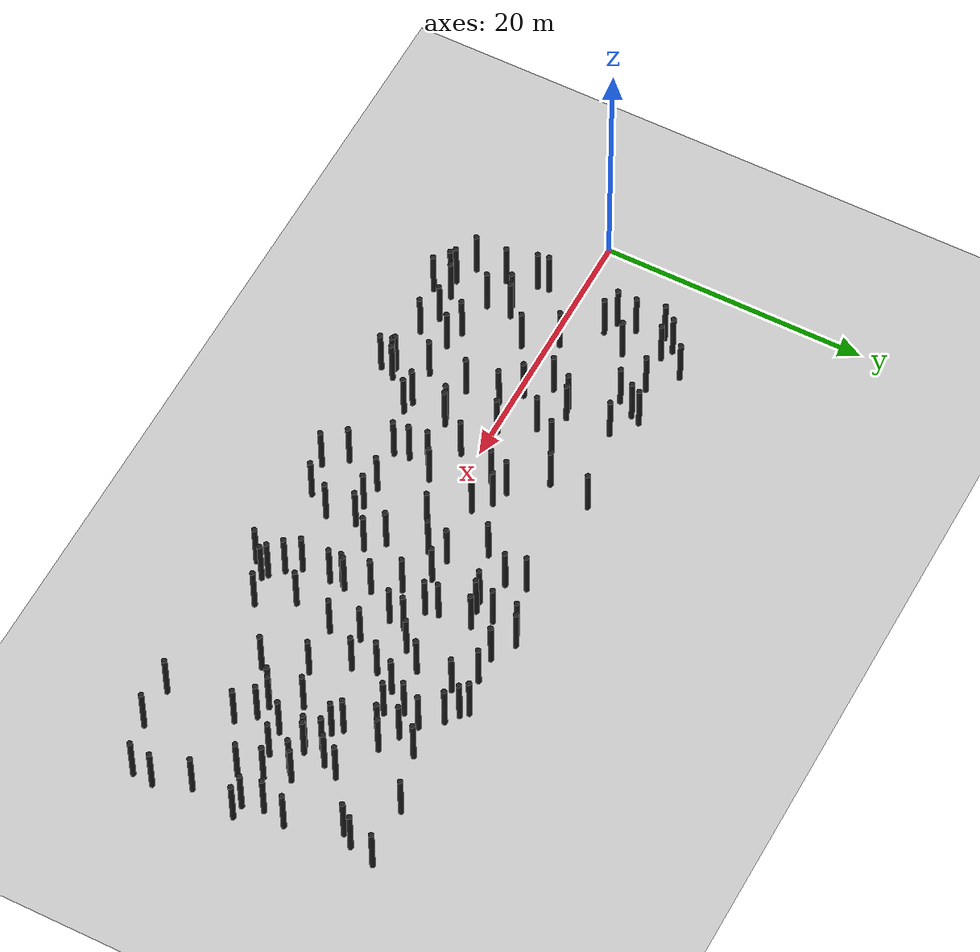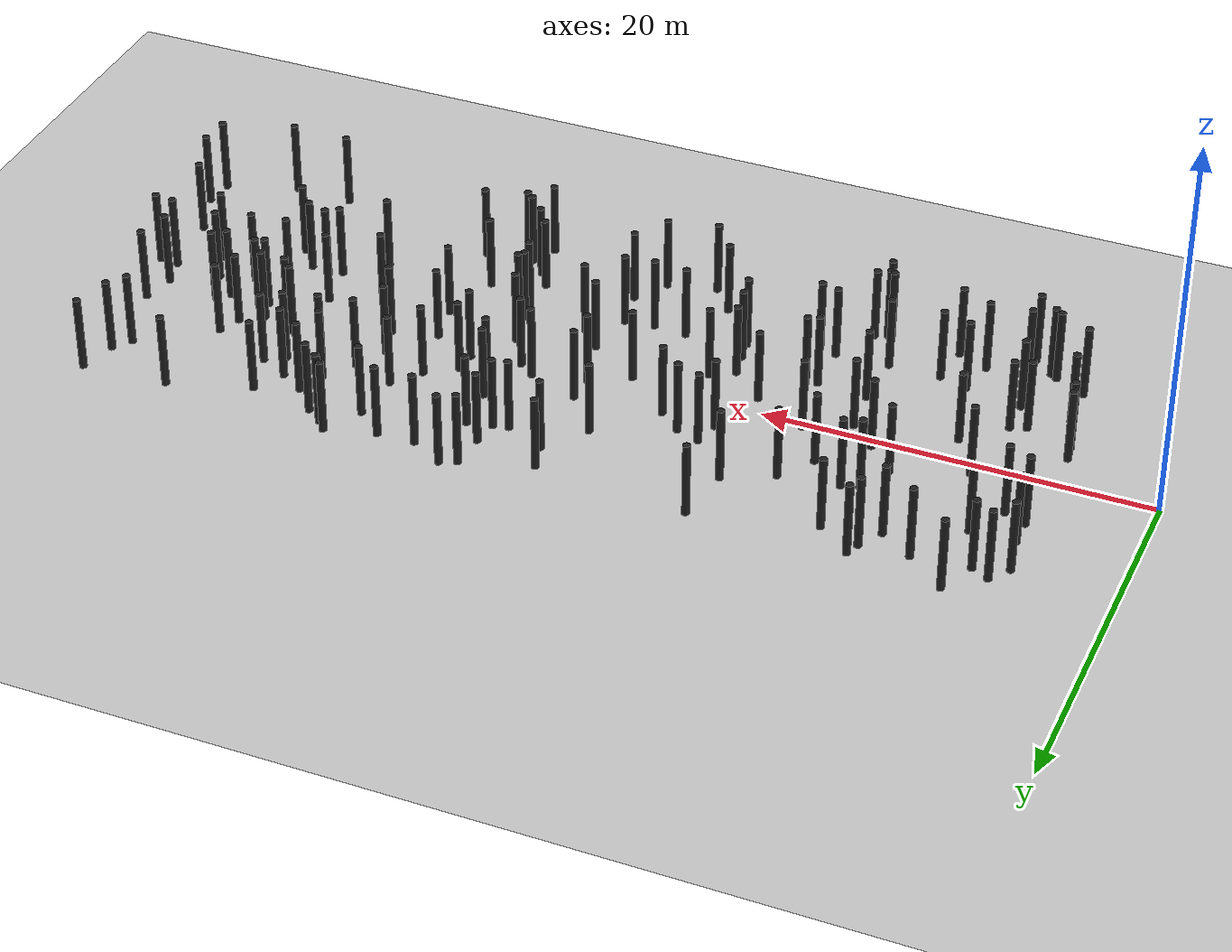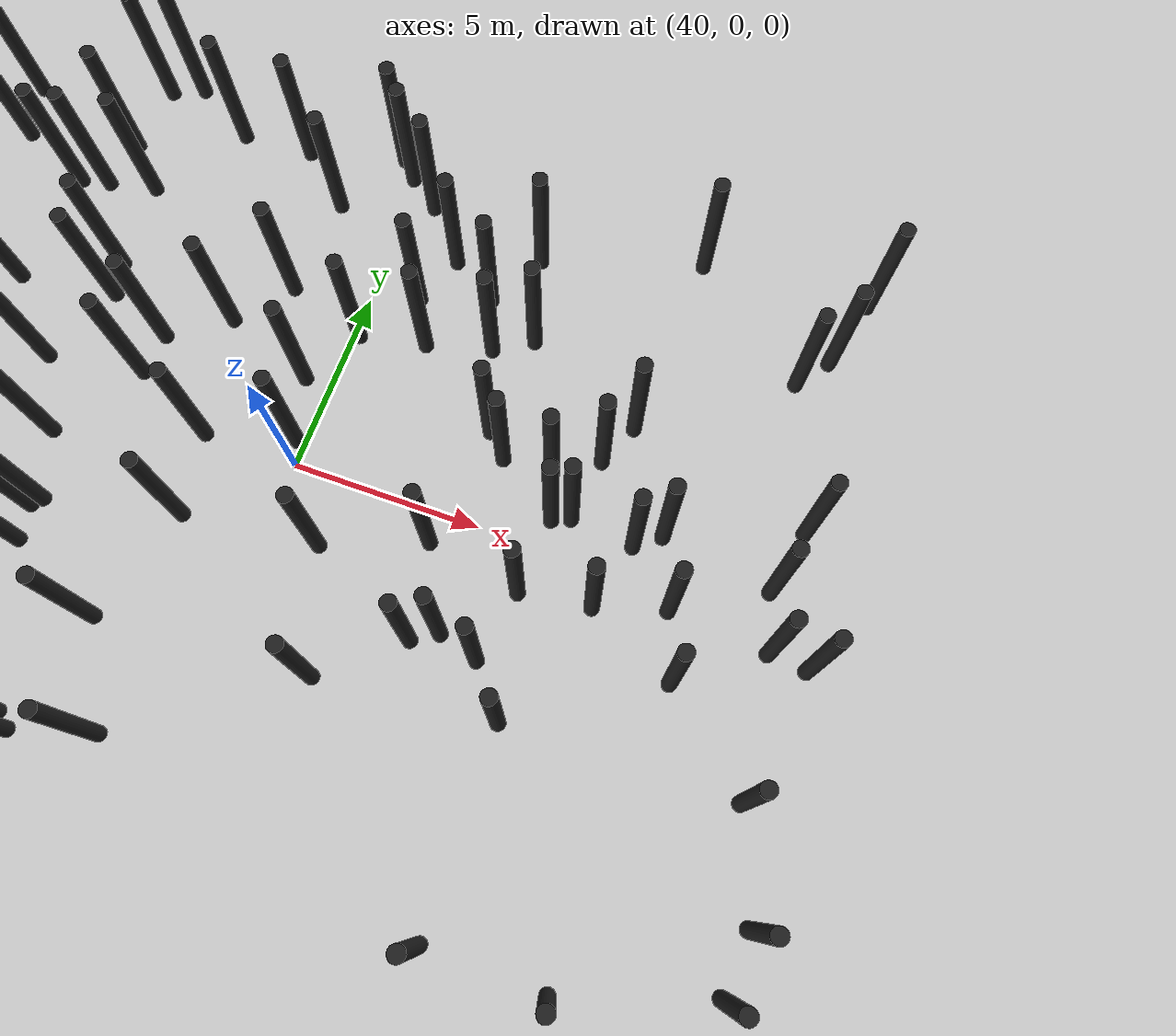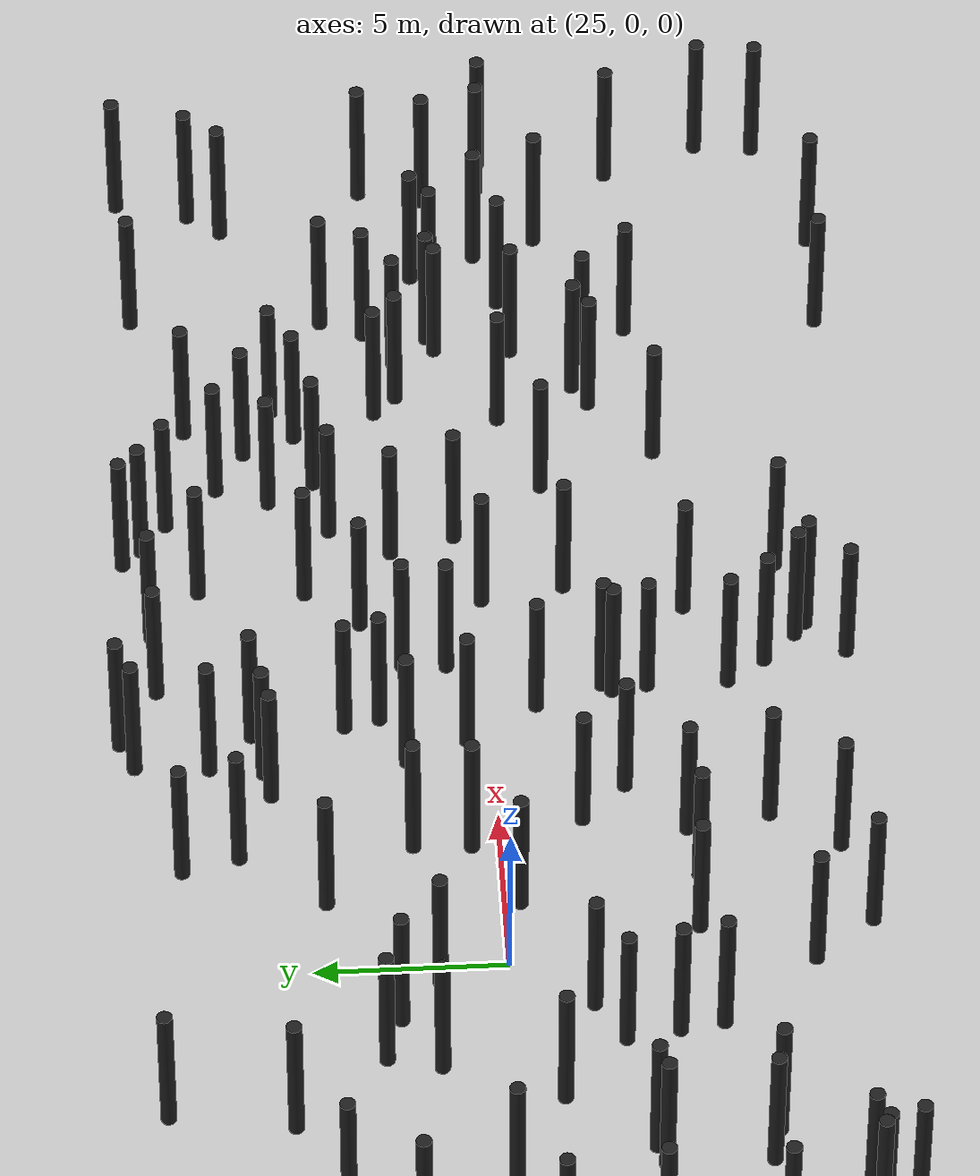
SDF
<sdf version="1.5">
 <world name="default">
  <plugin name="disable_physics" filename="libdisable_physics.so"/>
  <light name="sun" type="directional">
   <cast_shadows>0</cast_shadows>
   <pose>0 0 10 0 -0 0</pose>
   <diffuse>0.8 0.8 0.8 1</diffuse>
   <specular>0.2 0.2 0.2 1</specular>
   <attenuation>
    <range>1000</range>
    <constant>0.9</constant>
    <linear>0.01</linear>
    <quadratic>0.001</quadratic>
   </attenuation>
   <direction>-0.5 0.1 -0.9</direction>
  </light>
  <model name="ground_plane">
   <static>1</static>
   <link name="link">
    <collision name="collision">
     <geometry><plane><normal>0 0 1</normal><size>200 200</size></plane></geometry>
     <surface><friction><ode><mu>100</mu><mu2>50</mu2></ode></friction></surface>
    </collision>
    <visual name="visual">
     <cast_shadows>0</cast_shadows>
     <geometry><plane><normal>0 0 1</normal><size>200 200</size></plane></geometry>
     <material>
      <script><uri>file://media/materials/scripts/gazebo.material</uri><name>Gazebo/Grey</name></script>
     </material>
    </visual>
   </link>
  </model>
  <physics name="default_physics" default="0" type="ode">
   <max_step_size>0.001</max_step_size>
   <real_time_factor>1</real_time_factor>
   <real_time_update_rate>1000</real_time_update_rate>
   <gravity>0 0 -9.8</gravity>
   <magnetic_field>5.5645e-06 2.28758e-05 -4.23884e-05</magnetic_field>
  </physics>
  <scene>
   <ambient>0.4 0.4 0.4 1</ambient>
   <background>0.7 0.7 0.7 1</background>
   <shadows>0</shadows>
   <grid>false</grid>
  </scene>
  <spherical_coordinates>
   <surface_model>EARTH_WGS84</surface_model>
   <latitude_deg>0</latitude_deg>
   <longitude_deg>0</longitude_deg>
   <elevation>0</elevation>
   <heading_deg>0</heading_deg>
  </spherical_coordinates>
  <model name="forest_clone_0">
   <pose>47.8774 3.82717 -0.003373 0 -0 0</pose>
   <static>1</static>
   <link name="cylinder::link">
    <inertial>
     <mass>1</mass>
     <inertia><ixx>0.083</ixx><ixy>0</ixy><ixz>0</ixz><iyy>0.083</iyy><iyz>0</iyz><izz>0.083</izz></inertia>
    </inertial>
    <collision name="collision">
     <geometry><cylinder><radius>0.2</radius><length>4</length></cylinder></geometry>
    </collision>
    <visual name="visual">
     <geometry><cylinder><radius>0.2</radius><length>4</length></cylinder></geometry>
     <material>
      <script><uri>file://media/materials/scripts/gazebo.material</uri><name>Gazebo/Black</name></script>
     </material>
    </visual>
    <pose>0 0 2 0 -0 0</pose>
   </link>
  </model>
  <model name="forest_clone_1">
   <pose>14.5137 4.01554 -0.000699 0 -0 0</pose>
   <static>1</static>
   <link name="cylinder::link">
    <inertial>
     <mass>1</mass>
     <inertia><ixx>0.083</ixx><ixy>0</ixy><ixz>0</ixz><iyy>0.083</iyy><iyz>0</iyz><izz>0.083</izz></inertia>
    </inertial>
    <collision name="collision">
     <geometry><cylinder><radius>0.2</radius><length>4</length></cylinder></geometry>
    </collision>
    <visual name="visual">
     <geometry><cylinder><radius>0.2</radius><length>4</length></cylinder></geometry>
     <material>
      <script><uri>file://media/materials/scripts/gazebo.material</uri><name>Gazebo/Black</name></script>
     </material>
    </visual>
    <pose>0 0 2 0 -0 0</pose>
   </link>
  </model>
  <model name="forest_clone_2">
   <pose>39.7784 0.625088 -0.004027 0 -0 0</pose>
   <static>1</static>
   <link name="cylinder::link">
    <inertial>
     <mass>1</mass>
     <inertia><ixx>0.083</ixx><ixy>0</ixy><ixz>0</ixz><iyy>0.083</iyy><iyz>0</iyz><izz>0.083</izz></inertia>
    </inertial>
    <collision name="collision">
     <geometry><cylinder><radius>0.2</radius><length>4</length></cylinder></geometry>
    </collision>
    <visual name="visual">
     <geometry><cylinder><radius>0.2</radius><length>4</length></cylinder></geometry>
     <material>
      <script><uri>file://media/materials/scripts/gazebo.material</uri><name>Gazebo/Black</name></script>
     </material>
    </visual>
    <pose>0 0 2 0 -0 0</pose>
   </link>
  </model>
  <model name="forest_clone_3">
   <pose>27.0172 -0.385433 0.000234 0 -0 0</pose>
   <static>1</static>
   <link name="cylinder::link">
    <inertial>
     <mass>1</mass>
     <inertia><ixx>0.083</ixx><ixy>0</ixy><ixz>0</ixz><iyy>0.083</iyy><iyz>0</iyz><izz>0.083</izz></inertia>
    </inertial>
    <collision name="collision">
     <geometry><cylinder><radius>0.2</radius><length>4</length></cylinder></geometry>
    </collision>
    <visual name="visual">
     <geometry><cylinder><radius>0.2</radius><length>4</length></cylinder></geometry>
     <material>
      <script><uri>file://media/materials/scripts/gazebo.material</uri><name>Gazebo/Black</name></script>
     </material>
    </visual>
    <pose>0 0 2 0 -0 0</pose>
   </link>
  </model>
  <model name="forest_clone_4">
   <pose>41.9186 4.26882 0.003569 0 -0 0</pose>
   <static>1</static>
   <link name="cylinder::link">
    <inertial>
     <mass>1</mass>
     <inertia><ixx>0.083</ixx><ixy>0</ixy><ixz>0</ixz><iyy>0.083</iyy><iyz>0</iyz><izz>0.083</izz></inertia>
    </inertial>
    <collision name="collision">
     <geometry><cylinder><radius>0.2</radius><length>4</length></cylinder></geometry>
    </collision>
    <visual name="visual">
     <geometry><cylinder><radius>0.2</radius><length>4</length></cylinder></geometry>
     <material>
      <script><uri>file://media/materials/scripts/gazebo.material</uri><name>Gazebo/Black</name></script>
     </material>
    </visual>
    <pose>0 0 2 0 -0 0</pose>
   </link>
  </model>
  <model name="forest_clone_5">
   <pose>36.1798 -8.44092 -0.002637 0 -0 0</pose>
   <static>1</static>
   <link name="cylinder::link">
    <inertial>
     <mass>1</mass>
     <inertia><ixx>0.083</ixx><ixy>0</ixy><ixz>0</ixz><iyy>0.083</iyy><iyz>0</iyz><izz>0.083</izz></inertia>
    </inertial>
    <collision name="collision">
     <geometry><cylinder><radius>0.2</radius><length>4</length></cylinder></geometry>
    </collision>
    <visual name="visual">
     <geometry><cylinder><radius>0.2</radius><length>4</length></cylinder></geometry>
     <material>
      <script><uri>file://media/materials/scripts/gazebo.material</uri><name>Gazebo/Black</name></script>
     </material>
    </visual>
    <pose>0 0 2 0 -0 0</pose>
   </link>
  </model>
  <model name="forest_clone_6">
   <pose>51.4846 6.42449 0.004474 0 -0 0</pose>
   <static>1</static>
   <link name="cylinder::link">
    <inertial>
     <mass>1</mass>
     <inertia><ixx>0.083</ixx><ixy>0</ixy><ixz>0</ixz><iyy>0.083</iyy><iyz>0</iyz><izz>0.083</izz></inertia>
    </inertial>
    <collision name="collision">
     <geometry><cylinder><radius>0.2</radius><length>4</length></cylinder></geometry>
    </collision>
    <visual name="visual">
     <geometry><cylinder><radius>0.2</radius><length>4</length></cylinder></geometry>
     <material>
      <script><uri>file://media/materials/scripts/gazebo.material</uri><name>Gazebo/Black</name></script>
     </material>
    </visual>
    <pose>0 0 2 0 -0 0</pose>
   </link>
  </model>
  <model name="forest_clone_7">
   <pose>37.4556 0.018661 -0.002282 0 -0 0</pose>
   <static>1</static>
   <link name="cylinder::link">
    <inertial>
     <mass>1</mass>
     <inertia><ixx>0.083</ixx><ixy>0</ixy><ixz>0</ixz><iyy>0.083</iyy><iyz>0</iyz><izz>0.083</izz></inertia>
    </inertial>
    <collision name="collision">
     <geometry><cylinder><radius>0.2</radius><length>4</length></cylinder></geometry>
    </collision>
    <visual name="visual">
     <geometry><cylinder><radius>0.2</radius><length>4</length></cylinder></geometry>
     <material>
      <script><uri>file://media/materials/scripts/gazebo.material</uri><name>Gazebo/Black</name></script>
     </material>
    </visual>
    <pose>0 0 2 0 -0 0</pose>
   </link>
  </model>
  <model name="forest_clone_8">
   <pose>9.75084 7.86056 0.000782 0 -0 0</pose>
   <static>1</static>
   <link name="cylinder::link">
    <inertial>
     <mass>1</mass>
     <inertia><ixx>0.083</ixx><ixy>0</ixy><ixz>0</ixz><iyy>0.083</iyy><iyz>0</iyz><izz>0.083</izz></inertia>
    </inertial>
    <collision name="collision">
     <geometry><cylinder><radius>0.2</radius><length>4</length></cylinder></geometry>
    </collision>
    <visual name="visual">
     <geometry><cylinder><radius>0.2</radius><length>4</length></cylinder></geometry>
     <material>
      <script><uri>file://media/materials/scripts/gazebo.material</uri><name>Gazebo/Black</name></script>
     </material>
    </visual>
    <pose>0 0 2 0 -0 0</pose>
   </link>
  </model>
  <model name="forest_clone_9">
   <pose>48.8325 0.794509 0.003333 0 -0 0</pose>
   <static>1</static>
   <link name="cylinder::link">
    <inertial>
     <mass>1</mass>
     <inertia><ixx>0.083</ixx><ixy>0</ixy><ixz>0</ixz><iyy>0.083</iyy><iyz>0</iyz><izz>0.083</izz></inertia>
    </inertial>
    <collision name="collision">
     <geometry><cylinder><radius>0.2</radius><length>4</length></cylinder></geometry>
    </collision>
    <visual name="visual">
     <geometry><cylinder><radius>0.2</radius><length>4</length></cylinder></geometry>
     <material>
      <script><uri>file://media/materials/scripts/gazebo.material</uri><name>Gazebo/Black</name></script>
     </material>
    </visual>
    <pose>0 0 2 0 -0 0</pose>
   </link>
  </model>
  <model name="forest_clone_10">
   <pose>7.9358 -8.71365 -0.004995 0 -0 0</pose>
   <static>1</static>
   <link name="cylinder::link">
    <inertial>
     <mass>1</mass>
     <inertia><ixx>0.083</ixx><ixy>0</ixy><ixz>0</ixz><iyy>0.083</iyy><iyz>0</iyz><izz>0.083</izz></inertia>
    </inertial>
    <collision name="collision">
     <geometry><cylinder><radius>0.2</radius><length>4</length></cylinder></geometry>
    </collision>
    <visual name="visual">
     <geometry><cylinder><radius>0.2</radius><length>4</length></cylinder></geometry>
     <material>
      <script><uri>file://media/materials/scripts/gazebo.material</uri><name>Gazebo/Black</name></script>
     </material>
    </visual>
    <pose>0 0 2 0 -0 0</pose>
   </link>
  </model>
  <model name="forest_clone_11">
   <pose>34.0895 -3.20806 -0.003125 0 -0 0</pose>
   <static>1</static>
   <link name="cylinder::link">
    <inertial>
     <mass>1</mass>
     <inertia><ixx>0.083</ixx><ixy>0</ixy><ixz>0</ixz><iyy>0.083</iyy><iyz>0</iyz><izz>0.083</izz></inertia>
    </inertial>
    <collision name="collision">
     <geometry><cylinder><radius>0.2</radius><length>4</length></cylinder></geometry>
    </collision>
    <visual name="visual">
     <geometry><cylinder><radius>0.2</radius><length>4</length></cylinder></geometry>
     <material>
      <script><uri>file://media/materials/scripts/gazebo.material</uri><name>Gazebo/Black</name></script>
     </material>
    </visual>
    <pose>0 0 2 0 -0 0</pose>
   </link>
  </model>
  <model name="forest_clone_12">
   <pose>17.822 0.259165 0.002743 0 -0 0</pose>
   <static>1</static>
   <link name="cylinder::link">
    <inertial>
     <mass>1</mass>
     <inertia><ixx>0.083</ixx><ixy>0</ixy><ixz>0</ixz><iyy>0.083</iyy><iyz>0</iyz><izz>0.083</izz></inertia>
    </inertial>
    <collision name="collision">
     <geometry><cylinder><radius>0.2</radius><length>4</length></cylinder></geometry>
    </collision>
    <visual name="visual">
     <geometry><cylinder><radius>0.2</radius><length>4</length></cylinder></geometry>
     <material>
      <script><uri>file://media/materials/scripts/gazebo.material</uri><name>Gazebo/Black</name></script>
     </material>
    </visual>
    <pose>0 0 2 0 -0 0</pose>
   </link>
  </model>
  <model name="forest_clone_13">
   <pose>36.7887 3.25688 -0.000828 0 -0 0</pose>
   <static>1</static>
   <link name="cylinder::link">
    <inertial>
     <mass>1</mass>
     <inertia><ixx>0.083</ixx><ixy>0</ixy><ixz>0</ixz><iyy>0.083</iyy><iyz>0</iyz><izz>0.083</izz></inertia>
    </inertial>
    <collision name="collision">
     <geometry><cylinder><radius>0.2</radius><length>4</length></cylinder></geometry>
    </collision>
    <visual name="visual">
     <geometry><cylinder><radius>0.2</radius><length>4</length></cylinder></geometry>
     <material>
      <script><uri>file://media/materials/scripts/gazebo.material</uri><name>Gazebo/Black</name></script>
     </material>
    </visual>
    <pose>0 0 2 0 -0 0</pose>
   </link>
  </model>
  <model name="forest_clone_14">
   <pose>22.6307 -4.15857 -0.003113 0 -0 0</pose>
   <static>1</static>
   <link name="cylinder::link">
    <inertial>
     <mass>1</mass>
     <inertia><ixx>0.083</ixx><ixy>0</ixy><ixz>0</ixz><iyy>0.083</iyy><iyz>0</iyz><izz>0.083</izz></inertia>
    </inertial>
    <collision name="collision">
     <geometry><cylinder><radius>0.2</radius><length>4</length></cylinder></geometry>
    </collision>
    <visual name="visual">
     <geometry><cylinder><radius>0.2</radius><length>4</length></cylinder></geometry>
     <material>
      <script><uri>file://media/materials/scripts/gazebo.material</uri><name>Gazebo/Black</name></script>
     </material>
    </visual>
    <pose>0 0 2 0 -0 0</pose>
   </link>
  </model>
  <model name="forest_clone_15">
   <pose>5.15631 -2.23053 0.001161 0 -0 0</pose>
   <static>1</static>
   <link name="cylinder::link">
    <inertial>
     <mass>1</mass>
     <inertia><ixx>0.083</ixx><ixy>0</ixy><ixz>0</ixz><iyy>0.083</iyy><iyz>0</iyz><izz>0.083</izz></inertia>
    </inertial>
    <collision name="collision">
     <geometry><cylinder><radius>0.2</radius><length>4</length></cylinder></geometry>
    </collision>
    <visual name="visual">
     <geometry><cylinder><radius>0.2</radius><length>4</length></cylinder></geometry>
     <material>
      <script><uri>file://media/materials/scripts/gazebo.material</uri><name>Gazebo/Black</name></script>
     </material>
    </visual>
    <pose>0 0 2 0 -0 0</pose>
   </link>
  </model>
  <model name="forest_clone_16">
   <pose>29.0417 2.25112 0.003699 0 -0 0</pose>
   <static>1</static>
   <link name="cylinder::link">
    <inertial>
     <mass>1</mass>
     <inertia><ixx>0.083</ixx><ixy>0</ixy><ixz>0</ixz><iyy>0.083</iyy><iyz>0</iyz><izz>0.083</izz></inertia>
    </inertial>
    <collision name="collision">
     <geometry><cylinder><radius>0.2</radius><length>4</length></cylinder></geometry>
    </collision>
    <visual name="visual">
     <geometry><cylinder><radius>0.2</radius><length>4</length></cylinder></geometry>
     <material>
      <script><uri>file://media/materials/scripts/gazebo.material</uri><name>Gazebo/Black</name></script>
     </material>
    </visual>
    <pose>0 0 2 0 -0 0</pose>
   </link>
  </model>
  <model name="forest_clone_17">
   <pose>8.5037 -5.47283 -0.003477 0 -0 0</pose>
   <static>1</static>
   <link name="cylinder::link">
    <inertial>
     <mass>1</mass>
     <inertia><ixx>0.083</ixx><ixy>0</ixy><ixz>0</ixz><iyy>0.083</iyy><iyz>0</iyz><izz>0.083</izz></inertia>
    </inertial>
    <collision name="collision">
     <geometry><cylinder><radius>0.2</radius><length>4</length></cylinder></geometry>
    </collision>
    <visual name="visual">
     <geometry><cylinder><radius>0.2</radius><length>4</length></cylinder></geometry>
     <material>
      <script><uri>file://media/materials/scripts/gazebo.material</uri><name>Gazebo/Black</name></script>
     </material>
    </visual>
    <pose>0 0 2 0 -0 0</pose>
   </link>
  </model>
  <model name="forest_clone_18">
   <pose>28.9567 0.748121 0.004364 0 -0 0</pose>
   <static>1</static>
   <link name="cylinder::link">
    <inertial>
     <mass>1</mass>
     <inertia><ixx>0.083</ixx><ixy>0</ixy><ixz>0</ixz><iyy>0.083</iyy><iyz>0</iyz><izz>0.083</izz></inertia>
    </inertial>
    <collision name="collision">
     <geometry><cylinder><radius>0.2</radius><length>4</length></cylinder></geometry>
    </collision>
    <visual name="visual">
     <geometry><cylinder><radius>0.2</radius><length>4</length></cylinder></geometry>
     <material>
      <script><uri>file://media/materials/scripts/gazebo.material</uri><name>Gazebo/Black</name></script>
     </material>
    </visual>
    <pose>0 0 2 0 -0 0</pose>
   </link>
  </model>
  <model name="forest_clone_19">
   <pose>20.0552 5.6297 -0.002144 0 -0 0</pose>
   <static>1</static>
   <link name="cylinder::link">
    <inertial>
     <mass>1</mass>
     <inertia><ixx>0.083</ixx><ixy>0</ixy><ixz>0</ixz><iyy>0.083</iyy><iyz>0</iyz><izz>0.083</izz></inertia>
    </inertial>
    <collision name="collision">
     <geometry><cylinder><radius>0.2</radius><length>4</length></cylinder></geometry>
    </collision>
    <visual name="visual">
     <geometry><cylinder><radius>0.2</radius><length>4</length></cylinder></geometry>
     <material>
      <script><uri>file://media/materials/scripts/gazebo.material</uri><name>Gazebo/Black</name></script>
     </material>
    </visual>
    <pose>0 0 2 0 -0 0</pose>
   </link>
  </model>
  <model name="forest_clone_20">
   <pose>40.1537 3.9289 0.004832 0 -0 0</pose>
   <static>1</static>
   <link name="cylinder::link">
    <inertial>
     <mass>1</mass>
     <inertia><ixx>0.083</ixx><ixy>0</ixy><ixz>0</ixz><iyy>0.083</iyy><iyz>0</iyz><izz>0.083</izz></inertia>
    </inertial>
    <collision name="collision">
     <geometry><cylinder><radius>0.2</radius><length>4</length></cylinder></geometry>
    </collision>
    <visual name="visual">
     <geometry><cylinder><radius>0.2</radius><length>4</length></cylinder></geometry>
     <material>
      <script><uri>file://media/materials/scripts/gazebo.material</uri><name>Gazebo/Black</name></script>
     </material>
    </visual>
    <pose>0 0 2 0 -0 0</pose>
   </link>
  </model>
  <model name="forest_clone_21">
   <pose>27.7115 -5.01561 -0.001376 0 -0 0</pose>
   <static>1</static>
   <link name="cylinder::link">
    <inertial>
     <mass>1</mass>
     <inertia><ixx>0.083</ixx><ixy>0</ixy><ixz>0</ixz><iyy>0.083</iyy><iyz>0</iyz><izz>0.083</izz></inertia>
    </inertial>
    <collision name="collision">
     <geometry><cylinder><radius>0.2</radius><length>4</length></cylinder></geometry>
    </collision>
    <visual name="visual">
     <geometry><cylinder><radius>0.2</radius><length>4</length></cylinder></geometry>
     <material>
      <script><uri>file://media/materials/scripts/gazebo.material</uri><name>Gazebo/Black</name></script>
     </material>
    </visual>
    <pose>0 0 2 0 -0 0</pose>
   </link>
  </model>
  <model name="forest_clone_22">
   <pose>19.3052 -6.39627 0.002223 0 -0 0</pose>
   <static>1</static>
   <link name="cylinder::link">
    <inertial>
     <mass>1</mass>
     <inertia><ixx>0.083</ixx><ixy>0</ixy><ixz>0</ixz><iyy>0.083</iyy><iyz>0</iyz><izz>0.083</izz></inertia>
    </inertial>
    <collision name="collision">
     <geometry><cylinder><radius>0.2</radius><length>4</length></cylinder></geometry>
    </collision>
    <visual name="visual">
     <geometry><cylinder><radius>0.2</radius><length>4</length></cylinder></geometry>
     <material>
      <script><uri>file://media/materials/scripts/gazebo.material</uri><name>Gazebo/Black</name></script>
     </material>
    </visual>
    <pose>0 0 2 0 -0 0</pose>
   </link>
  </model>
  <model name="forest_clone_23">
   <pose>15.7641 -3.30514 -0.001914 0 -0 0</pose>
   <static>1</static>
   <link name="cylinder::link">
    <inertial>
     <mass>1</mass>
     <inertia><ixx>0.083</ixx><ixy>0</ixy><ixz>0</ixz><iyy>0.083</iyy><iyz>0</iyz><izz>0.083</izz></inertia>
    </inertial>
    <collision name="collision">
     <geometry><cylinder><radius>0.2</radius><length>4</length></cylinder></geometry>
    </collision>
    <visual name="visual">
     <geometry><cylinder><radius>0.2</radius><length>4</length></cylinder></geometry>
     <material>
      <script><uri>file://media/materials/scripts/gazebo.material</uri><name>Gazebo/Black</name></script>
     </material>
    </visual>
    <pose>0 0 2 0 -0 0</pose>
   </link>
  </model>
  <model name="forest_clone_24">
   <pose>7.577 -8.45598 -0.001071 0 -0 0</pose>
   <static>1</static>
   <link name="cylinder::link">
    <inertial>
     <mass>1</mass>
     <inertia><ixx>0.083</ixx><ixy>0</ixy><ixz>0</ixz><iyy>0.083</iyy><iyz>0</iyz><izz>0.083</izz></inertia>
    </inertial>
    <collision name="collision">
     <geometry><cylinder><radius>0.2</radius><length>4</length></cylinder></geometry>
    </collision>
    <visual name="visual">
     <geometry><cylinder><radius>0.2</radius><length>4</length></cylinder></geometry>
     <material>
      <script><uri>file://media/materials/scripts/gazebo.material</uri><name>Gazebo/Black</name></script>
     </material>
    </visual>
    <pose>0 0 2 0 -0 0</pose>
   </link>
  </model>
  <model name="forest_clone_25">
   <pose>6.67753 2.99067 -0.003952 0 -0 0</pose>
   <static>1</static>
   <link name="cylinder::link">
    <inertial>
     <mass>1</mass>
     <inertia><ixx>0.083</ixx><ixy>0</ixy><ixz>0</ixz><iyy>0.083</iyy><iyz>0</iyz><izz>0.083</izz></inertia>
    </inertial>
    <collision name="collision">
     <geometry><cylinder><radius>0.2</radius><length>4</length></cylinder></geometry>
    </collision>
    <visual name="visual">
     <geometry><cylinder><radius>0.2</radius><length>4</length></cylinder></geometry>
     <material>
      <script><uri>file://media/materials/scripts/gazebo.material</uri><name>Gazebo/Black</name></script>
     </material>
    </visual>
    <pose>0 0 2 0 -0 0</pose>
   </link>
  </model>
  <model name="forest_clone_26">
   <pose>6.83102 7.58389 0.004837 0 -0 0</pose>
   <static>1</static>
   <link name="cylinder::link">
    <inertial>
     <mass>1</mass>
     <inertia><ixx>0.083</ixx><ixy>0</ixy><ixz>0</ixz><iyy>0.083</iyy><iyz>0</iyz><izz>0.083</izz></inertia>
    </inertial>
    <collision name="collision">
     <geometry><cylinder><radius>0.2</radius><length>4</length></cylinder></geometry>
    </collision>
    <visual name="visual">
     <geometry><cylinder><radius>0.2</radius><length>4</length></cylinder></geometry>
     <material>
      <script><uri>file://media/materials/scripts/gazebo.material</uri><name>Gazebo/Black</name></script>
     </material>
    </visual>
    <pose>0 0 2 0 -0 0</pose>
   </link>
  </model>
  <model name="forest_clone_27">
   <pose>35.2688 2.22048 -0.003432 0 -0 0</pose>
   <static>1</static>
   <link name="cylinder::link">
    <inertial>
     <mass>1</mass>
     <inertia><ixx>0.083</ixx><ixy>0</ixy><ixz>0</ixz><iyy>0.083</iyy><iyz>0</iyz><izz>0.083</izz></inertia>
    </inertial>
    <collision name="collision">
     <geometry><cylinder><radius>0.2</radius><length>4</length></cylinder></geometry>
    </collision>
    <visual name="visual">
     <geometry><cylinder><radius>0.2</radius><length>4</length></cylinder></geometry>
     <material>
      <script><uri>file://media/materials/scripts/gazebo.material</uri><name>Gazebo/Black</name></script>
     </material>
    </visual>
    <pose>0 0 2 0 -0 0</pose>
   </link>
  </model>
  <model name="forest_clone_28">
   <pose>28.4963 -8.72486 -0.003639 0 -0 0</pose>
   <static>1</static>
   <link name="cylinder::link">
    <inertial>
     <mass>1</mass>
     <inertia><ixx>0.083</ixx><ixy>0</ixy><ixz>0</ixz><iyy>0.083</iyy><iyz>0</iyz><izz>0.083</izz></inertia>
    </inertial>
    <collision name="collision">
     <geometry><cylinder><radius>0.2</radius><length>4</length></cylinder></geometry>
    </collision>
    <visual name="visual">
     <geometry><cylinder><radius>0.2</radius><length>4</length></cylinder></geometry>
     <material>
      <script><uri>file://media/materials/scripts/gazebo.material</uri><name>Gazebo/Black</name></script>
     </material>
    </visual>
    <pose>0 0 2 0 -0 0</pose>
   </link>
  </model>
  <model name="forest_clone_29">
   <pose>14.199 0.46277 0.000633 0 -0 0</pose>
   <static>1</static>
   <link name="cylinder::link">
    <inertial>
     <mass>1</mass>
     <inertia><ixx>0.083</ixx><ixy>0</ixy><ixz>0</ixz><iyy>0.083</iyy><iyz>0</iyz><izz>0.083</izz></inertia>
    </inertial>
    <collision name="collision">
     <geometry><cylinder><radius>0.2</radius><length>4</length></cylinder></geometry>
    </collision>
    <visual name="visual">
     <geometry><cylinder><radius>0.2</radius><length>4</length></cylinder></geometry>
     <material>
      <script><uri>file://media/materials/scripts/gazebo.material</uri><name>Gazebo/Black</name></script>
     </material>
    </visual>
    <pose>0 0 2 0 -0 0</pose>
   </link>
  </model>
  <model name="forest_clone_30">
   <pose>35.1356 -9.4416 0.002527 0 -0 0</pose>
   <static>1</static>
   <link name="cylinder::link">
    <inertial>
     <mass>1</mass>
     <inertia><ixx>0.083</ixx><ixy>0</ixy><ixz>0</ixz><iyy>0.083</iyy><iyz>0</iyz><izz>0.083</izz></inertia>
    </inertial>
    <collision name="collision">
     <geometry><cylinder><radius>0.2</radius><length>4</length></cylinder></geometry>
    </collision>
    <visual name="visual">
     <geometry><cylinder><radius>0.2</radius><length>4</length></cylinder></geometry>
     <material>
      <script><uri>file://media/materials/scripts/gazebo.material</uri><name>Gazebo/Black</name></script>
     </material>
    </visual>
    <pose>0 0 2 0 -0 0</pose>
   </link>
  </model>
  <model name="forest_clone_31">
   <pose>32.5848 0.669089 -0.004582 0 -0 0</pose>
   <static>1</static>
   <link name="cylinder::link">
    <inertial>
     <mass>1</mass>
     <inertia><ixx>0.083</ixx><ixy>0</ixy><ixz>0</ixz><iyy>0.083</iyy><iyz>0</iyz><izz>0.083</izz></inertia>
    </inertial>
    <collision name="collision">
     <geometry><cylinder><radius>0.2</radius><length>4</length></cylinder></geometry>
    </collision>
    <visual name="visual">
     <geometry><cylinder><radius>0.2</radius><length>4</length></cylinder></geometry>
     <material>
      <script><uri>file://media/materials/scripts/gazebo.material</uri><name>Gazebo/Black</name></script>
     </material>
    </visual>
    <pose>0 0 2 0 -0 0</pose>
   </link>
  </model>
  <model name="forest_clone_32">
   <pose>46.2905 1.91843 0.004142 0 -0 0</pose>
   <static>1</static>
   <link name="cylinder::link">
    <inertial>
     <mass>1</mass>
     <inertia><ixx>0.083</ixx><ixy>0</ixy><ixz>0</ixz><iyy>0.083</iyy><iyz>0</iyz><izz>0.083</izz></inertia>
    </inertial>
    <collision name="collision">
     <geometry><cylinder><radius>0.2</radius><length>4</length></cylinder></geometry>
    </collision>
    <visual name="visual">
     <geometry><cylinder><radius>0.2</radius><length>4</length></cylinder></geometry>
     <material>
      <script><uri>file://media/materials/scripts/gazebo.material</uri><name>Gazebo/Black</name></script>
     </material>
    </visual>
    <pose>0 0 2 0 -0 0</pose>
   </link>
  </model>
  <model name="forest_clone_33">
   <pose>37.8248 -2.16475 0.001127 0 -0 0</pose>
   <static>1</static>
   <link name="cylinder::link">
    <inertial>
     <mass>1</mass>
     <inertia><ixx>0.083</ixx><ixy>0</ixy><ixz>0</ixz><iyy>0.083</iyy><iyz>0</iyz><izz>0.083</izz></inertia>
    </inertial>
    <collision name="collision">
     <geometry><cylinder><radius>0.2</radius><length>4</length></cylinder></geometry>
    </collision>
    <visual name="visual">
     <geometry><cylinder><radius>0.2</radius><length>4</length></cylinder></geometry>
     <material>
      <script><uri>file://media/materials/scripts/gazebo.material</uri><name>Gazebo/Black</name></script>
     </material>
    </visual>
    <pose>0 0 2 0 -0 0</pose>
   </link>
  </model>
  <model name="forest_clone_34">
   <pose>36.6583 8.76226 0.004077 0 -0 0</pose>
   <static>1</static>
   <link name="cylinder::link">
    <inertial>
     <mass>1</mass>
     <inertia><ixx>0.083</ixx><ixy>0</ixy><ixz>0</ixz><iyy>0.083</iyy><iyz>0</iyz><izz>0.083</izz></inertia>
    </inertial>
    <collision name="collision">
     <geometry><cylinder><radius>0.2</radius><length>4</length></cylinder></geometry>
    </collision>
    <visual name="visual">
     <geometry><cylinder><radius>0.2</radius><length>4</length></cylinder></geometry>
     <material>
      <script><uri>file://media/materials/scripts/gazebo.material</uri><name>Gazebo/Black</name></script>
     </material>
    </visual>
    <pose>0 0 2 0 -0 0</pose>
   </link>
  </model>
  <model name="forest_clone_35">
   <pose>38.3017 -7.80817 0.004289 0 -0 0</pose>
   <static>1</static>
   <link name="cylinder::link">
    <inertial>
     <mass>1</mass>
     <inertia><ixx>0.083</ixx><ixy>0</ixy><ixz>0</ixz><iyy>0.083</iyy><iyz>0</iyz><izz>0.083</izz></inertia>
    </inertial>
    <collision name="collision">
     <geometry><cylinder><radius>0.2</radius><length>4</length></cylinder></geometry>
    </collision>
    <visual name="visual">
     <geometry><cylinder><radius>0.2</radius><length>4</length></cylinder></geometry>
     <material>
      <script><uri>file://media/materials/scripts/gazebo.material</uri><name>Gazebo/Black</name></script>
     </material>
    </visual>
    <pose>0 0 2 0 -0 0</pose>
   </link>
  </model>
  <model name="forest_clone_36">
   <pose>15.5521 -0.809213 0.003796 0 -0 0</pose>
   <static>1</static>
   <link name="cylinder::link">
    <inertial>
     <mass>1</mass>
     <inertia><ixx>0.083</ixx><ixy>0</ixy><ixz>0</ixz><iyy>0.083</iyy><iyz>0</iyz><izz>0.083</izz></inertia>
    </inertial>
    <collision name="collision">
     <geometry><cylinder><radius>0.2</radius><length>4</length></cylinder></geometry>
    </collision>
    <visual name="visual">
     <geometry><cylinder><radius>0.2</radius><length>4</length></cylinder></geometry>
     <material>
      <script><uri>file://media/materials/scripts/gazebo.material</uri><name>Gazebo/Black</name></script>
     </material>
    </visual>
    <pose>0 0 2 0 -0 0</pose>
   </link>
  </model>
  <model name="forest_clone_37">
   <pose>16.7115 -9.62116 -0.003995 0 -0 0</pose>
   <static>1</static>
   <link name="cylinder::link">
    <inertial>
     <mass>1</mass>
     <inertia><ixx>0.083</ixx><ixy>0</ixy><ixz>0</ixz><iyy>0.083</iyy><iyz>0</iyz><izz>0.083</izz></inertia>
    </inertial>
    <collision name="collision">
     <geometry><cylinder><radius>0.2</radius><length>4</length></cylinder></geometry>
    </collision>
    <visual name="visual">
     <geometry><cylinder><radius>0.2</radius><length>4</length></cylinder></geometry>
     <material>
      <script><uri>file://media/materials/scripts/gazebo.material</uri><name>Gazebo/Black</name></script>
     </material>
    </visual>
    <pose>0 0 2 0 -0 0</pose>
   </link>
  </model>
  <model name="forest_clone_38">
   <pose>34.2289 -4.12915 0.002319 0 -0 0</pose>
   <static>1</static>
   <link name="cylinder::link">
    <inertial>
     <mass>1</mass>
     <inertia><ixx>0.083</ixx><ixy>0</ixy><ixz>0</ixz><iyy>0.083</iyy><iyz>0</iyz><izz>0.083</izz></inertia>
    </inertial>
    <collision name="collision">
     <geometry><cylinder><radius>0.2</radius><length>4</length></cylinder></geometry>
    </collision>
    <visual name="visual">
     <geometry><cylinder><radius>0.2</radius><length>4</length></cylinder></geometry>
     <material>
      <script><uri>file://media/materials/scripts/gazebo.material</uri><name>Gazebo/Black</name></script>
     </material>
    </visual>
    <pose>0 0 2 0 -0 0</pose>
   </link>
  </model>
  <model name="forest_clone_39">
   <pose>41.8105 6.88139 -0.00208 0 -0 0</pose>
   <static>1</static>
   <link name="cylinder::link">
    <inertial>
     <mass>1</mass>
     <inertia><ixx>0.083</ixx><ixy>0</ixy><ixz>0</ixz><iyy>0.083</iyy><iyz>0</iyz><izz>0.083</izz></inertia>
    </inertial>
    <collision name="collision">
     <geometry><cylinder><radius>0.2</radius><length>4</length></cylinder></geometry>
    </collision>
    <visual name="visual">
     <geometry><cylinder><radius>0.2</radius><length>4</length></cylinder></geometry>
     <material>
      <script><uri>file://media/materials/scripts/gazebo.material</uri><name>Gazebo/Black</name></script>
     </material>
    </visual>
    <pose>0 0 2 0 -0 0</pose>
   </link>
  </model>
  <model name="forest_clone_40">
   <pose>41.2674 5.5002 0.002673 0 -0 0</pose>
   <static>1</static>
   <link name="cylinder::link">
    <inertial>
     <mass>1</mass>
     <inertia><ixx>0.083</ixx><ixy>0</ixy><ixz>0</ixz><iyy>0.083</iyy><iyz>0</iyz><izz>0.083</izz></inertia>
    </inertial>
    <collision name="collision">
     <geometry><cylinder><radius>0.2</radius><length>4</length></cylinder></geometry>
    </collision>
    <visual name="visual">
     <geometry><cylinder><radius>0.2</radius><length>4</length></cylinder></geometry>
     <material>
      <script><uri>file://media/materials/scripts/gazebo.material</uri><name>Gazebo/Black</name></script>
     </material>
    </visual>
    <pose>0 0 2 0 -0 0</pose>
   </link>
  </model>
  <model name="forest_clone_41">
   <pose>44.9711 1.92104 -0.002985 0 -0 0</pose>
   <static>1</static>
   <link name="cylinder::link">
    <inertial>
     <mass>1</mass>
     <inertia><ixx>0.083</ixx><ixy>0</ixy><ixz>0</ixz><iyy>0.083</iyy><iyz>0</iyz><izz>0.083</izz></inertia>
    </inertial>
    <collision name="collision">
     <geometry><cylinder><radius>0.2</radius><length>4</length></cylinder></geometry>
    </collision>
    <visual name="visual">
     <geometry><cylinder><radius>0.2</radius><length>4</length></cylinder></geometry>
     <material>
      <script><uri>file://media/materials/scripts/gazebo.material</uri><name>Gazebo/Black</name></script>
     </material>
    </visual>
    <pose>0 0 2 0 -0 0</pose>
   </link>
  </model>
  <model name="forest_clone_42">
   <pose>33.6852 -1.19974 -0.000456 0 -0 0</pose>
   <static>1</static>
   <link name="cylinder::link">
    <inertial>
     <mass>1</mass>
     <inertia><ixx>0.083</ixx><ixy>0</ixy><ixz>0</ixz><iyy>0.083</iyy><iyz>0</iyz><izz>0.083</izz></inertia>
    </inertial>
    <collision name="collision">
     <geometry><cylinder><radius>0.2</radius><length>4</length></cylinder></geometry>
    </collision>
    <visual name="visual">
     <geometry><cylinder><radius>0.2</radius><length>4</length></cylinder></geometry>
     <material>
      <script><uri>file://media/materials/scripts/gazebo.material</uri><name>Gazebo/Black</name></script>
     </material>
    </visual>
    <pose>0 0 2 0 -0 0</pose>
   </link>
  </model>
  <model name="forest_clone_43">
   <pose>52.1522 7.30841 -0.000244 0 -0 0</pose>
   <static>1</static>
   <link name="cylinder::link">
    <inertial>
     <mass>1</mass>
     <inertia><ixx>0.083</ixx><ixy>0</ixy><ixz>0</ixz><iyy>0.083</iyy><iyz>0</iyz><izz>0.083</izz></inertia>
    </inertial>
    <collision name="collision">
     <geometry><cylinder><radius>0.2</radius><length>4</length></cylinder></geometry>
    </collision>
    <visual name="visual">
     <geometry><cylinder><radius>0.2</radius><length>4</length></cylinder></geometry>
     <material>
      <script><uri>file://media/materials/scripts/gazebo.material</uri><name>Gazebo/Black</name></script>
     </material>
    </visual>
    <pose>0 0 2 0 -0 0</pose>
   </link>
  </model>
  <model name="forest_clone_44">
   <pose>15.6181 -6.32503 -0.002952 0 -0 0</pose>
   <static>1</static>
   <link name="cylinder::link">
    <inertial>
     <mass>1</mass>
     <inertia><ixx>0.083</ixx><ixy>0</ixy><ixz>0</ixz><iyy>0.083</iyy><iyz>0</iyz><izz>0.083</izz></inertia>
    </inertial>
    <collision name="collision">
     <geometry><cylinder><radius>0.2</radius><length>4</length></cylinder></geometry>
    </collision>
    <visual name="visual">
     <geometry><cylinder><radius>0.2</radius><length>4</length></cylinder></geometry>
     <material>
      <script><uri>file://media/materials/scripts/gazebo.material</uri><name>Gazebo/Black</name></script>
     </material>
    </visual>
    <pose>0 0 2 0 -0 0</pose>
   </link>
  </model>
  <model name="forest_clone_45">
   <pose>39.2487 9.43692 0.00181 0 -0 0</pose>
   <static>1</static>
   <link name="cylinder::link">
    <inertial>
     <mass>1</mass>
     <inertia><ixx>0.083</ixx><ixy>0</ixy><ixz>0</ixz><iyy>0.083</iyy><iyz>0</iyz><izz>0.083</izz></inertia>
    </inertial>
    <collision name="collision">
     <geometry><cylinder><radius>0.2</radius><length>4</length></cylinder></geometry>
    </collision>
    <visual name="visual">
     <geometry><cylinder><radius>0.2</radius><length>4</length></cylinder></geometry>
     <material>
      <script><uri>file://media/materials/scripts/gazebo.material</uri><name>Gazebo/Black</name></script>
     </material>
    </visual>
    <pose>0 0 2 0 -0 0</pose>
   </link>
  </model>
  <model name="forest_clone_46">
   <pose>50.1674 -0.477466 0.002206 0 -0 0</pose>
   <static>1</static>
   <link name="cylinder::link">
    <inertial>
     <mass>1</mass>
     <inertia><ixx>0.083</ixx><ixy>0</ixy><ixz>0</ixz><iyy>0.083</iyy><iyz>0</iyz><izz>0.083</izz></inertia>
    </inertial>
    <collision name="collision">
     <geometry><cylinder><radius>0.2</radius><length>4</length></cylinder></geometry>
    </collision>
    <visual name="visual">
     <geometry><cylinder><radius>0.2</radius><length>4</length></cylinder></geometry>
     <material>
      <script><uri>file://media/materials/scripts/gazebo.material</uri><name>Gazebo/Black</name></script>
     </material>
    </visual>
    <pose>0 0 2 0 -0 0</pose>
   </link>
  </model>
  <model name="forest_clone_47">
   <pose>50.2921 -9.67215 0.004809 0 -0 0</pose>
   <static>1</static>
   <link name="cylinder::link">
    <inertial>
     <mass>1</mass>
     <inertia><ixx>0.083</ixx><ixy>0</ixy><ixz>0</ixz><iyy>0.083</iyy><iyz>0</iyz><izz>0.083</izz></inertia>
    </inertial>
    <collision name="collision">
     <geometry><cylinder><radius>0.2</radius><length>4</length></cylinder></geometry>
    </collision>
    <visual name="visual">
     <geometry><cylinder><radius>0.2</radius><length>4</length></cylinder></geometry>
     <material>
      <script><uri>file://media/materials/scripts/gazebo.material</uri><name>Gazebo/Black</name></script>
     </material>
    </visual>
    <pose>0 0 2 0 -0 0</pose>
   </link>
  </model>
  <model name="forest_clone_48">
   <pose>47.1435 0.969786 -0.003645 0 -0 0</pose>
   <static>1</static>
   <link name="cylinder::link">
    <inertial>
     <mass>1</mass>
     <inertia><ixx>0.083</ixx><ixy>0</ixy><ixz>0</ixz><iyy>0.083</iyy><iyz>0</iyz><izz>0.083</izz></inertia>
    </inertial>
    <collision name="collision">
     <geometry><cylinder><radius>0.2</radius><length>4</length></cylinder></geometry>
    </collision>
    <visual name="visual">
     <geometry><cylinder><radius>0.2</radius><length>4</length></cylinder></geometry>
     <material>
      <script><uri>file://media/materials/scripts/gazebo.material</uri><name>Gazebo/Black</name></script>
     </material>
    </visual>
    <pose>0 0 2 0 -0 0</pose>
   </link>
  </model>
  <model name="forest_clone_49">
   <pose>39.7175 8.92321 0.003022 0 -0 0</pose>
   <static>1</static>
   <link name="cylinder::link">
    <inertial>
     <mass>1</mass>
     <inertia><ixx>0.083</ixx><ixy>0</ixy><ixz>0</ixz><iyy>0.083</iyy><iyz>0</iyz><izz>0.083</izz></inertia>
    </inertial>
    <collision name="collision">
     <geometry><cylinder><radius>0.2</radius><length>4</length></cylinder></geometry>
    </collision>
    <visual name="visual">
     <geometry><cylinder><radius>0.2</radius><length>4</length></cylinder></geometry>
     <material>
      <script><uri>file://media/materials/scripts/gazebo.material</uri><name>Gazebo/Black</name></script>
     </material>
    </visual>
    <pose>0 0 2 0 -0 0</pose>
   </link>
  </model>
  <model name="forest_clone_50">
   <pose>42.5434 -4.87461 0.002801 0 -0 0</pose>
   <static>1</static>
   <link name="cylinder::link">
    <inertial>
     <mass>1</mass>
     <inertia><ixx>0.083</ixx><ixy>0</ixy><ixz>0</ixz><iyy>0.083</iyy><iyz>0</iyz><izz>0.083</izz></inertia>
    </inertial>
    <collision name="collision">
     <geometry><cylinder><radius>0.2</radius><length>4</length></cylinder></geometry>
    </collision>
    <visual name="visual">
     <geometry><cylinder><radius>0.2</radius><length>4</length></cylinder></geometry>
     <material>
      <script><uri>file://media/materials/scripts/gazebo.material</uri><name>Gazebo/Black</name></script>
     </material>
    </visual>
    <pose>0 0 2 0 -0 0</pose>
   </link>
  </model>
  <model name="forest_clone_51">
   <pose>12.7447 2.09471 -0.001897 0 -0 0</pose>
   <static>1</static>
   <link name="cylinder::link">
    <inertial>
     <mass>1</mass>
     <inertia><ixx>0.083</ixx><ixy>0</ixy><ixz>0</ixz><iyy>0.083</iyy><iyz>0</iyz><izz>0.083</izz></inertia>
    </inertial>
    <collision name="collision">
     <geometry><cylinder><radius>0.2</radius><length>4</length></cylinder></geometry>
    </collision>
    <visual name="visual">
     <geometry><cylinder><radius>0.2</radius><length>4</length></cylinder></geometry>
     <material>
      <script><uri>file://media/materials/scripts/gazebo.material</uri><name>Gazebo/Black</name></script>
     </material>
    </visual>
    <pose>0 0 2 0 -0 0</pose>
   </link>
  </model>
  <model name="forest_clone_52">
   <pose>16.2916 -8.64391 0.003343 0 -0 0</pose>
   <static>1</static>
   <link name="cylinder::link">
    <inertial>
     <mass>1</mass>
     <inertia><ixx>0.083</ixx><ixy>0</ixy><ixz>0</ixz><iyy>0.083</iyy><iyz>0</iyz><izz>0.083</izz></inertia>
    </inertial>
    <collision name="collision">
     <geometry><cylinder><radius>0.2</radius><length>4</length></cylinder></geometry>
    </collision>
    <visual name="visual">
     <geometry><cylinder><radius>0.2</radius><length>4</length></cylinder></geometry>
     <material>
      <script><uri>file://media/materials/scripts/gazebo.material</uri><name>Gazebo/Black</name></script>
     </material>
    </visual>
    <pose>0 0 2 0 -0 0</pose>
   </link>
  </model>
  <model name="forest_clone_53">
   <pose>31.286 2.29813 0.756441 0 -0 0</pose>
   <static>1</static>
   <link name="cylinder::link">
    <inertial>
     <mass>1</mass>
     <inertia><ixx>0.083</ixx><ixy>0</ixy><ixz>0</ixz><iyy>0.083</iyy><iyz>0</iyz><izz>0.083</izz></inertia>
    </inertial>
    <collision name="collision">
     <geometry><cylinder><radius>0.2</radius><length>4</length></cylinder></geometry>
    </collision>
    <visual name="visual">
     <geometry><cylinder><radius>0.2</radius><length>4</length></cylinder></geometry>
     <material>
      <script><uri>file://media/materials/scripts/gazebo.material</uri><name>Gazebo/Black</name></script>
     </material>
    </visual>
    <pose>0 0 2 0 -0 0</pose>
   </link>
  </model>
  <model name="forest_clone_54">
   <pose>47.2161 -9.63317 -0.004522 0 -0 0</pose>
   <static>1</static>
   <link name="cylinder::link">
    <inertial>
     <mass>1</mass>
     <inertia><ixx>0.083</ixx><ixy>0</ixy><ixz>0</ixz><iyy>0.083</iyy><iyz>0</iyz><izz>0.083</izz></inertia>
    </inertial>
    <collision name="collision">
     <geometry><cylinder><radius>0.2</radius><length>4</length></cylinder></geometry>
    </collision>
    <visual name="visual">
     <geometry><cylinder><radius>0.2</radius><length>4</length></cylinder></geometry>
     <material>
      <script><uri>file://media/materials/scripts/gazebo.material</uri><name>Gazebo/Black</name></script>
     </material>
    </visual>
    <pose>0 0 2 0 -0 0</pose>
   </link>
  </model>
  <model name="forest_clone_55">
   <pose>38.1316 7.47372 0.000722 0 -0 0</pose>
   <static>1</static>
   <link name="cylinder::link">
    <inertial>
     <mass>1</mass>
     <inertia><ixx>0.083</ixx><ixy>0</ixy><ixz>0</ixz><iyy>0.083</iyy><iyz>0</iyz><izz>0.083</izz></inertia>
    </inertial>
    <collision name="collision">
     <geometry><cylinder><radius>0.2</radius><length>4</length></cylinder></geometry>
    </collision>
    <visual name="visual">
     <geometry><cylinder><radius>0.2</radius><length>4</length></cylinder></geometry>
     <material>
      <script><uri>file://media/materials/scripts/gazebo.material</uri><name>Gazebo/Black</name></script>
     </material>
    </visual>
    <pose>0 0 2 0 -0 0</pose>
   </link>
  </model>
  <model name="forest_clone_56">
   <pose>22.0934 3.26191 0.00056 0 -0 0</pose>
   <static>1</static>
   <link name="cylinder::link">
    <inertial>
     <mass>1</mass>
     <inertia><ixx>0.083</ixx><ixy>0</ixy><ixz>0</ixz><iyy>0.083</iyy><iyz>0</iyz><izz>0.083</izz></inertia>
    </inertial>
    <collision name="collision">
     <geometry><cylinder><radius>0.2</radius><length>4</length></cylinder></geometry>
    </collision>
    <visual name="visual">
     <geometry><cylinder><radius>0.2</radius><length>4</length></cylinder></geometry>
     <material>
      <script><uri>file://media/materials/scripts/gazebo.material</uri><name>Gazebo/Black</name></script>
     </material>
    </visual>
    <pose>0 0 2 0 -0 0</pose>
   </link>
  </model>
  <model name="forest_clone_57">
   <pose>34.3083 -2.96168 0.001023 0 -0 0</pose>
   <static>1</static>
   <link name="cylinder::link">
    <inertial>
     <mass>1</mass>
     <inertia><ixx>0.083</ixx><ixy>0</ixy><ixz>0</ixz><iyy>0.083</iyy><iyz>0</iyz><izz>0.083</izz></inertia>
    </inertial>
    <collision name="collision">
     <geometry><cylinder><radius>0.2</radius><length>4</length></cylinder></geometry>
    </collision>
    <visual name="visual">
     <geometry><cylinder><radius>0.2</radius><length>4</length></cylinder></geometry>
     <material>
      <script><uri>file://media/materials/scripts/gazebo.material</uri><name>Gazebo/Black</name></script>
     </material>
    </visual>
    <pose>0 0 2 0 -0 0</pose>
   </link>
  </model>
  <model name="forest_clone_58">
   <pose>9.11435 0.693786 0.004038 0 -0 0</pose>
   <static>1</static>
   <link name="cylinder::link">
    <inertial>
     <mass>1</mass>
     <inertia><ixx>0.083</ixx><ixy>0</ixy><ixz>0</ixz><iyy>0.083</iyy><iyz>0</iyz><izz>0.083</izz></inertia>
    </inertial>
    <collision name="collision">
     <geometry><cylinder><radius>0.2</radius><length>4</length></cylinder></geometry>
    </collision>
    <visual name="visual">
     <geometry><cylinder><radius>0.2</radius><length>4</length></cylinder></geometry>
     <material>
      <script><uri>file://media/materials/scripts/gazebo.material</uri><name>Gazebo/Black</name></script>
     </material>
    </visual>
    <pose>0 0 2 0 -0 0</pose>
   </link>
  </model>
  <model name="forest_clone_59">
   <pose>32.101 9.32027 0.000197 0 -0 0</pose>
   <static>1</static>
   <link name="cylinder::link">
    <inertial>
     <mass>1</mass>
     <inertia><ixx>0.083</ixx><ixy>0</ixy><ixz>0</ixz><iyy>0.083</iyy><iyz>0</iyz><izz>0.083</izz></inertia>
    </inertial>
    <collision name="collision">
     <geometry><cylinder><radius>0.2</radius><length>4</length></cylinder></geometry>
    </collision>
    <visual name="visual">
     <geometry><cylinder><radius>0.2</radius><length>4</length></cylinder></geometry>
     <material>
      <script><uri>file://media/materials/scripts/gazebo.material</uri><name>Gazebo/Black</name></script>
     </material>
    </visual>
    <pose>0 0 2 0 -0 0</pose>
   </link>
  </model>
  <model name="forest_clone_60">
   <pose>12.2292 8.00595 0.003583 0 -0 0</pose>
   <static>1</static>
   <link name="cylinder::link">
    <inertial>
     <mass>1</mass>
     <inertia><ixx>0.083</ixx><ixy>0</ixy><ixz>0</ixz><iyy>0.083</iyy><iyz>0</iyz><izz>0.083</izz></inertia>
    </inertial>
    <collision name="collision">
     <geometry><cylinder><radius>0.2</radius><length>4</length></cylinder></geometry>
    </collision>
    <visual name="visual">
     <geometry><cylinder><radius>0.2</radius><length>4</length></cylinder></geometry>
     <material>
      <script><uri>file://media/materials/scripts/gazebo.material</uri><name>Gazebo/Black</name></script>
     </material>
    </visual>
    <pose>0 0 2 0 -0 0</pose>
   </link>
  </model>
  <model name="forest_clone_61">
   <pose>44.6094 5.31662 -7.9e-05 0 -0 0</pose>
   <static>1</static>
   <link name="cylinder::link">
    <inertial>
     <mass>1</mass>
     <inertia><ixx>0.083</ixx><ixy>0</ixy><ixz>0</ixz><iyy>0.083</iyy><iyz>0</iyz><izz>0.083</izz></inertia>
    </inertial>
    <collision name="collision">
     <geometry><cylinder><radius>0.2</radius><length>4</length></cylinder></geometry>
    </collision>
    <visual name="visual">
     <geometry><cylinder><radius>0.2</radius><length>4</length></cylinder></geometry>
     <material>
      <script><uri>file://media/materials/scripts/gazebo.material</uri><name>Gazebo/Black</name></script>
     </material>
    </visual>
    <pose>0 0 2 0 -0 0</pose>
   </link>
  </model>
  <model name="forest_clone_62">
   <pose>7.79568 4.9876 0.002756 0 -0 0</pose>
   <static>1</static>
   <link name="cylinder::link">
    <inertial>
     <mass>1</mass>
     <inertia><ixx>0.083</ixx><ixy>0</ixy><ixz>0</ixz><iyy>0.083</iyy><iyz>0</iyz><izz>0.083</izz></inertia>
    </inertial>
    <collision name="collision">
     <geometry><cylinder><radius>0.2</radius><length>4</length></cylinder></geometry>
    </collision>
    <visual name="visual">
     <geometry><cylinder><radius>0.2</radius><length>4</length></cylinder></geometry>
     <material>
      <script><uri>file://media/materials/scripts/gazebo.material</uri><name>Gazebo/Black</name></script>
     </material>
    </visual>
    <pose>0 0 2 0 -0 0</pose>
   </link>
  </model>
  <model name="forest_clone_63">
   <pose>49.4635 1.2827 0.003801 0 -0 0</pose>
   <static>1</static>
   <link name="cylinder::link">
    <inertial>
     <mass>1</mass>
     <inertia><ixx>0.083</ixx><ixy>0</ixy><ixz>0</ixz><iyy>0.083</iyy><iyz>0</iyz><izz>0.083</izz></inertia>
    </inertial>
    <collision name="collision">
     <geometry><cylinder><radius>0.2</radius><length>4</length></cylinder></geometry>
    </collision>
    <visual name="visual">
     <geometry><cylinder><radius>0.2</radius><length>4</length></cylinder></geometry>
     <material>
      <script><uri>file://media/materials/scripts/gazebo.material</uri><name>Gazebo/Black</name></script>
     </material>
    </visual>
    <pose>0 0 2 0 -0 0</pose>
   </link>
  </model>
  <model name="forest_clone_64">
   <pose>43.6352 4.71826 0.003077 0 -0 0</pose>
   <static>1</static>
   <link name="cylinder::link">
    <inertial>
     <mass>1</mass>
     <inertia><ixx>0.083</ixx><ixy>0</ixy><ixz>0</ixz><iyy>0.083</iyy><iyz>0</iyz><izz>0.083</izz></inertia>
    </inertial>
    <collision name="collision">
     <geometry><cylinder><radius>0.2</radius><length>4</length></cylinder></geometry>
    </collision>
    <visual name="visual">
     <geometry><cylinder><radius>0.2</radius><length>4</length></cylinder></geometry>
     <material>
      <script><uri>file://media/materials/scripts/gazebo.material</uri><name>Gazebo/Black</name></script>
     </material>
    </visual>
    <pose>0 0 2 0 -0 0</pose>
   </link>
  </model>
  <model name="forest_clone_65">
   <pose>16.3187 2.63364 -0.000558 0 -0 0</pose>
   <static>1</static>
   <link name="cylinder::link">
    <inertial>
     <mass>1</mass>
     <inertia><ixx>0.083</ixx><ixy>0</ixy><ixz>0</ixz><iyy>0.083</iyy><iyz>0</iyz><izz>0.083</izz></inertia>
    </inertial>
    <collision name="collision">
     <geometry><cylinder><radius>0.2</radius><length>4</length></cylinder></geometry>
    </collision>
    <visual name="visual">
     <geometry><cylinder><radius>0.2</radius><length>4</length></cylinder></geometry>
     <material>
      <script><uri>file://media/materials/scripts/gazebo.material</uri><name>Gazebo/Black</name></script>
     </material>
    </visual>
    <pose>0 0 2 0 -0 0</pose>
   </link>
  </model>
  <model name="forest_clone_66">
   <pose>52.6861 9.25518 0.00349 0 -0 0</pose>
   <static>1</static>
   <link name="cylinder::link">
    <inertial>
     <mass>1</mass>
     <inertia><ixx>0.083</ixx><ixy>0</ixy><ixz>0</ixz><iyy>0.083</iyy><iyz>0</iyz><izz>0.083</izz></inertia>
    </inertial>
    <collision name="collision">
     <geometry><cylinder><radius>0.2</radius><length>4</length></cylinder></geometry>
    </collision>
    <visual name="visual">
     <geometry><cylinder><radius>0.2</radius><length>4</length></cylinder></geometry>
     <material>
      <script><uri>file://media/materials/scripts/gazebo.material</uri><name>Gazebo/Black</name></script>
     </material>
    </visual>
    <pose>0 0 2 0 -0 0</pose>
   </link>
  </model>
  <model name="forest_clone_67">
   <pose>41.4226 -1.78511 0.049028 0 -0 0</pose>
   <static>1</static>
   <link name="cylinder::link">
    <inertial>
     <mass>1</mass>
     <inertia><ixx>0.083</ixx><ixy>0</ixy><ixz>0</ixz><iyy>0.083</iyy><iyz>0</iyz><izz>0.083</izz></inertia>
    </inertial>
    <collision name="collision">
     <geometry><cylinder><radius>0.2</radius><length>4</length></cylinder></geometry>
    </collision>
    <visual name="visual">
     <geometry><cylinder><radius>0.2</radius><length>4</length></cylinder></geometry>
     <material>
      <script><uri>file://media/materials/scripts/gazebo.material</uri><name>Gazebo/Black</name></script>
     </material>
    </visual>
    <pose>0 0 2 0 -0 0</pose>
   </link>
  </model>
  <model name="forest_clone_68">
   <pose>52.4022 0.812248 -0.004377 0 -0 0</pose>
   <static>1</static>
   <link name="cylinder::link">
    <inertial>
     <mass>1</mass>
     <inertia><ixx>0.083</ixx><ixy>0</ixy><ixz>0</ixz><iyy>0.083</iyy><iyz>0</iyz><izz>0.083</izz></inertia>
    </inertial>
    <collision name="collision">
     <geometry><cylinder><radius>0.2</radius><length>4</length></cylinder></geometry>
    </collision>
    <visual name="visual">
     <geometry><cylinder><radius>0.2</radius><length>4</length></cylinder></geometry>
     <material>
      <script><uri>file://media/materials/scripts/gazebo.material</uri><name>Gazebo/Black</name></script>
     </material>
    </visual>
    <pose>0 0 2 0 -0 0</pose>
   </link>
  </model>
  <model name="forest_clone_69">
   <pose>12.6681 -8.64279 -0.004902 0 -0 0</pose>
   <static>1</static>
   <link name="cylinder::link">
    <inertial>
     <mass>1</mass>
     <inertia><ixx>0.083</ixx><ixy>0</ixy><ixz>0</ixz><iyy>0.083</iyy><iyz>0</iyz><izz>0.083</izz></inertia>
    </inertial>
    <collision name="collision">
     <geometry><cylinder><radius>0.2</radius><length>4</length></cylinder></geometry>
    </collision>
    <visual name="visual">
     <geometry><cylinder><radius>0.2</radius><length>4</length></cylinder></geometry>
     <material>
      <script><uri>file://media/materials/scripts/gazebo.material</uri><name>Gazebo/Black</name></script>
     </material>
    </visual>
    <pose>0 0 2 0 -0 0</pose>
   </link>
  </model>
  <model name="forest_clone_70">
   <pose>44.4505 -3.25783 -0.004054 0 -0 0</pose>
   <static>1</static>
   <link name="cylinder::link">
    <inertial>
     <mass>1</mass>
     <inertia><ixx>0.083</ixx><ixy>0</ixy><ixz>0</ixz><iyy>0.083</iyy><iyz>0</iyz><izz>0.083</izz></inertia>
    </inertial>
    <collision name="collision">
     <geometry><cylinder><radius>0.2</radius><length>4</length></cylinder></geometry>
    </collision>
    <visual name="visual">
     <geometry><cylinder><radius>0.2</radius><length>4</length></cylinder></geometry>
     <material>
      <script><uri>file://media/materials/scripts/gazebo.material</uri><name>Gazebo/Black</name></script>
     </material>
    </visual>
    <pose>0 0 2 0 -0 0</pose>
   </link>
  </model>
  <model name="forest_clone_71">
   <pose>17.5765 4.42719 -0.001861 0 -0 0</pose>
   <static>1</static>
   <link name="cylinder::link">
    <inertial>
     <mass>1</mass>
     <inertia><ixx>0.083</ixx><ixy>0</ixy><ixz>0</ixz><iyy>0.083</iyy><iyz>0</iyz><izz>0.083</izz></inertia>
    </inertial>
    <collision name="collision">
     <geometry><cylinder><radius>0.2</radius><length>4</length></cylinder></geometry>
    </collision>
    <visual name="visual">
     <geometry><cylinder><radius>0.2</radius><length>4</length></cylinder></geometry>
     <material>
      <script><uri>file://media/materials/scripts/gazebo.material</uri><name>Gazebo/Black</name></script>
     </material>
    </visual>
    <pose>0 0 2 0 -0 0</pose>
   </link>
  </model>
  <model name="forest_clone_72">
   <pose>53.7753 -0.792174 -0.003367 0 -0 0</pose>
   <static>1</static>
   <link name="cylinder::link">
    <inertial>
     <mass>1</mass>
     <inertia><ixx>0.083</ixx><ixy>0</ixy><ixz>0</ixz><iyy>0.083</iyy><iyz>0</iyz><izz>0.083</izz></inertia>
    </inertial>
    <collision name="collision">
     <geometry><cylinder><radius>0.2</radius><length>4</length></cylinder></geometry>
    </collision>
    <visual name="visual">
     <geometry><cylinder><radius>0.2</radius><length>4</length></cylinder></geometry>
     <material>
      <script><uri>file://media/materials/scripts/gazebo.material</uri><name>Gazebo/Black</name></script>
     </material>
    </visual>
    <pose>0 0 2 0 -0 0</pose>
   </link>
  </model>
  <model name="forest_clone_73">
   <pose>43.093 6.10205 -0.001918 0 -0 0</pose>
   <static>1</static>
   <link name="cylinder::link">
    <inertial>
     <mass>1</mass>
     <inertia><ixx>0.083</ixx><ixy>0</ixy><ixz>0</ixz><iyy>0.083</iyy><iyz>0</iyz><izz>0.083</izz></inertia>
    </inertial>
    <collision name="collision">
     <geometry><cylinder><radius>0.2</radius><length>4</length></cylinder></geometry>
    </collision>
    <visual name="visual">
     <geometry><cylinder><radius>0.2</radius><length>4</length></cylinder></geometry>
     <material>
      <script><uri>file://media/materials/scripts/gazebo.material</uri><name>Gazebo/Black</name></script>
     </material>
    </visual>
    <pose>0 0 2 0 -0 0</pose>
   </link>
  </model>
  <model name="forest_clone_74">
   <pose>40.6022 8.25454 -0.004001 0 -0 0</pose>
   <static>1</static>
   <link name="cylinder::link">
    <inertial>
     <mass>1</mass>
     <inertia><ixx>0.083</ixx><ixy>0</ixy><ixz>0</ixz><iyy>0.083</iyy><iyz>0</iyz><izz>0.083</izz></inertia>
    </inertial>
    <collision name="collision">
     <geometry><cylinder><radius>0.2</radius><length>4</length></cylinder></geometry>
    </collision>
    <visual name="visual">
     <geometry><cylinder><radius>0.2</radius><length>4</length></cylinder></geometry>
     <material>
      <script><uri>file://media/materials/scripts/gazebo.material</uri><name>Gazebo/Black</name></script>
     </material>
    </visual>
    <pose>0 0 2 0 -0 0</pose>
   </link>
  </model>
  <model name="forest_clone_75">
   <pose>8.49426 -3.59042 -0.003223 0 -0 0</pose>
   <static>1</static>
   <link name="cylinder::link">
    <inertial>
     <mass>1</mass>
     <inertia><ixx>0.083</ixx><ixy>0</ixy><ixz>0</ixz><iyy>0.083</iyy><iyz>0</iyz><izz>0.083</izz></inertia>
    </inertial>
    <collision name="collision">
     <geometry><cylinder><radius>0.2</radius><length>4</length></cylinder></geometry>
    </collision>
    <visual name="visual">
     <geometry><cylinder><radius>0.2</radius><length>4</length></cylinder></geometry>
     <material>
      <script><uri>file://media/materials/scripts/gazebo.material</uri><name>Gazebo/Black</name></script>
     </material>
    </visual>
    <pose>0 0 2 0 -0 0</pose>
   </link>
  </model>
  <model name="forest_clone_76">
   <pose>34.6908 8.67813 -0.001923 0 -0 0</pose>
   <static>1</static>
   <link name="cylinder::link">
    <inertial>
     <mass>1</mass>
     <inertia><ixx>0.083</ixx><ixy>0</ixy><ixz>0</ixz><iyy>0.083</iyy><iyz>0</iyz><izz>0.083</izz></inertia>
    </inertial>
    <collision name="collision">
     <geometry><cylinder><radius>0.2</radius><length>4</length></cylinder></geometry>
    </collision>
    <visual name="visual">
     <geometry><cylinder><radius>0.2</radius><length>4</length></cylinder></geometry>
     <material>
      <script><uri>file://media/materials/scripts/gazebo.material</uri><name>Gazebo/Black</name></script>
     </material>
    </visual>
    <pose>0 0 2 0 -0 0</pose>
   </link>
  </model>
  <model name="forest_clone_77">
   <pose>47.3836 2.68623 -0.003206 0 -0 0</pose>
   <static>1</static>
   <link name="cylinder::link">
    <inertial>
     <mass>1</mass>
     <inertia><ixx>0.083</ixx><ixy>0</ixy><ixz>0</ixz><iyy>0.083</iyy><iyz>0</iyz><izz>0.083</izz></inertia>
    </inertial>
    <collision name="collision">
     <geometry><cylinder><radius>0.2</radius><length>4</length></cylinder></geometry>
    </collision>
    <visual name="visual">
     <geometry><cylinder><radius>0.2</radius><length>4</length></cylinder></geometry>
     <material>
      <script><uri>file://media/materials/scripts/gazebo.material</uri><name>Gazebo/Black</name></script>
     </material>
    </visual>
    <pose>0 0 2 0 -0 0</pose>
   </link>
  </model>
  <model name="forest_clone_78">
   <pose>36.9069 -5.275 0.004699 0 -0 0</pose>
   <static>1</static>
   <link name="cylinder::link">
    <inertial>
     <mass>1</mass>
     <inertia><ixx>0.083</ixx><ixy>0</ixy><ixz>0</ixz><iyy>0.083</iyy><iyz>0</iyz><izz>0.083</izz></inertia>
    </inertial>
    <collision name="collision">
     <geometry><cylinder><radius>0.2</radius><length>4</length></cylinder></geometry>
    </collision>
    <visual name="visual">
     <geometry><cylinder><radius>0.2</radius><length>4</length></cylinder></geometry>
     <material>
      <script><uri>file://media/materials/scripts/gazebo.material</uri><name>Gazebo/Black</name></script>
     </material>
    </visual>
    <pose>0 0 2 0 -0 0</pose>
   </link>
  </model>
  <model name="forest_clone_79">
   <pose>21.7627 1.88539 0.004949 0 -0 0</pose>
   <static>1</static>
   <link name="cylinder::link">
    <inertial>
     <mass>1</mass>
     <inertia><ixx>0.083</ixx><ixy>0</ixy><ixz>0</ixz><iyy>0.083</iyy><iyz>0</iyz><izz>0.083</izz></inertia>
    </inertial>
    <collision name="collision">
     <geometry><cylinder><radius>0.2</radius><length>4</length></cylinder></geometry>
    </collision>
    <visual name="visual">
     <geometry><cylinder><radius>0.2</radius><length>4</length></cylinder></geometry>
     <material>
      <script><uri>file://media/materials/scripts/gazebo.material</uri><name>Gazebo/Black</name></script>
     </material>
    </visual>
    <pose>0 0 2 0 -0 0</pose>
   </link>
  </model>
  <model name="forest_clone_80">
   <pose>39.2798 2.32573 0.000206 0 -0 0</pose>
   <static>1</static>
   <link name="cylinder::link">
    <inertial>
     <mass>1</mass>
     <inertia><ixx>0.083</ixx><ixy>0</ixy><ixz>0</ixz><iyy>0.083</iyy><iyz>0</iyz><izz>0.083</izz></inertia>
    </inertial>
    <collision name="collision">
     <geometry><cylinder><radius>0.2</radius><length>4</length></cylinder></geometry>
    </collision>
    <visual name="visual">
     <geometry><cylinder><radius>0.2</radius><length>4</length></cylinder></geometry>
     <material>
      <script><uri>file://media/materials/scripts/gazebo.material</uri><name>Gazebo/Black</name></script>
     </material>
    </visual>
    <pose>0 0 2 0 -0 0</pose>
   </link>
  </model>
  <model name="forest_clone_81">
   <pose>50.7425 -2.16861 0.000282 0 -0 0</pose>
   <static>1</static>
   <link name="cylinder::link">
    <inertial>
     <mass>1</mass>
     <inertia><ixx>0.083</ixx><ixy>0</ixy><ixz>0</ixz><iyy>0.083</iyy><iyz>0</iyz><izz>0.083</izz></inertia>
    </inertial>
    <collision name="collision">
     <geometry><cylinder><radius>0.2</radius><length>4</length></cylinder></geometry>
    </collision>
    <visual name="visual">
     <geometry><cylinder><radius>0.2</radius><length>4</length></cylinder></geometry>
     <material>
      <script><uri>file://media/materials/scripts/gazebo.material</uri><name>Gazebo/Black</name></script>
     </material>
    </visual>
    <pose>0 0 2 0 -0 0</pose>
   </link>
  </model>
  <model name="forest_clone_82">
   <pose>18.385 -3.50208 5.1e-05 0 -0 0</pose>
   <static>1</static>
   <link name="cylinder::link">
    <inertial>
     <mass>1</mass>
     <inertia><ixx>0.083</ixx><ixy>0</ixy><ixz>0</ixz><iyy>0.083</iyy><iyz>0</iyz><izz>0.083</izz></inertia>
    </inertial>
    <collision name="collision">
     <geometry><cylinder><radius>0.2</radius><length>4</length></cylinder></geometry>
    </collision>
    <visual name="visual">
     <geometry><cylinder><radius>0.2</radius><length>4</length></cylinder></geometry>
     <material>
      <script><uri>file://media/materials/scripts/gazebo.material</uri><name>Gazebo/Black</name></script>
     </material>
    </visual>
    <pose>0 0 2 0 -0 0</pose>
   </link>
  </model>
  <model name="forest_clone_83">
   <pose>17.1378 -8.48723 -0.00473 0 -0 0</pose>
   <static>1</static>
   <link name="cylinder::link">
    <inertial>
     <mass>1</mass>
     <inertia><ixx>0.083</ixx><ixy>0</ixy><ixz>0</ixz><iyy>0.083</iyy><iyz>0</iyz><izz>0.083</izz></inertia>
    </inertial>
    <collision name="collision">
     <geometry><cylinder><radius>0.2</radius><length>4</length></cylinder></geometry>
    </collision>
    <visual name="visual">
     <geometry><cylinder><radius>0.2</radius><length>4</length></cylinder></geometry>
     <material>
      <script><uri>file://media/materials/scripts/gazebo.material</uri><name>Gazebo/Black</name></script>
     </material>
    </visual>
    <pose>0 0 2 0 -0 0</pose>
   </link>
  </model>
  <model name="forest_clone_84">
   <pose>32.9401 9.6855 -0.004697 0 -0 0</pose>
   <static>1</static>
   <link name="cylinder::link">
    <inertial>
     <mass>1</mass>
     <inertia><ixx>0.083</ixx><ixy>0</ixy><ixz>0</ixz><iyy>0.083</iyy><iyz>0</iyz><izz>0.083</izz></inertia>
    </inertial>
    <collision name="collision">
     <geometry><cylinder><radius>0.2</radius><length>4</length></cylinder></geometry>
    </collision>
    <visual name="visual">
     <geometry><cylinder><radius>0.2</radius><length>4</length></cylinder></geometry>
     <material>
      <script><uri>file://media/materials/scripts/gazebo.material</uri><name>Gazebo/Black</name></script>
     </material>
    </visual>
    <pose>0 0 2 0 -0 0</pose>
   </link>
  </model>
  <model name="forest_clone_85">
   <pose>23.34 2.83419 0.002213 0 -0 0</pose>
   <static>1</static>
   <link name="cylinder::link">
    <inertial>
     <mass>1</mass>
     <inertia><ixx>0.083</ixx><ixy>0</ixy><ixz>0</ixz><iyy>0.083</iyy><iyz>0</iyz><izz>0.083</izz></inertia>
    </inertial>
    <collision name="collision">
     <geometry><cylinder><radius>0.2</radius><length>4</length></cylinder></geometry>
    </collision>
    <visual name="visual">
     <geometry><cylinder><radius>0.2</radius><length>4</length></cylinder></geometry>
     <material>
      <script><uri>file://media/materials/scripts/gazebo.material</uri><name>Gazebo/Black</name></script>
     </material>
    </visual>
    <pose>0 0 2 0 -0 0</pose>
   </link>
  </model>
  <model name="forest_clone_86">
   <pose>12.9302 -6.35618 -0.001206 0 -0 0</pose>
   <static>1</static>
   <link name="cylinder::link">
    <inertial>
     <mass>1</mass>
     <inertia><ixx>0.083</ixx><ixy>0</ixy><ixz>0</ixz><iyy>0.083</iyy><iyz>0</iyz><izz>0.083</izz></inertia>
    </inertial>
    <collision name="collision">
     <geometry><cylinder><radius>0.2</radius><length>4</length></cylinder></geometry>
    </collision>
    <visual name="visual">
     <geometry><cylinder><radius>0.2</radius><length>4</length></cylinder></geometry>
     <material>
      <script><uri>file://media/materials/scripts/gazebo.material</uri><name>Gazebo/Black</name></script>
     </material>
    </visual>
    <pose>0 0 2 0 -0 0</pose>
   </link>
  </model>
  <model name="forest_clone_87">
   <pose>31.9507 7.38285 0.002783 0 -0 0</pose>
   <static>1</static>
   <link name="cylinder::link">
    <inertial>
     <mass>1</mass>
     <inertia><ixx>0.083</ixx><ixy>0</ixy><ixz>0</ixz><iyy>0.083</iyy><iyz>0</iyz><izz>0.083</izz></inertia>
    </inertial>
    <collision name="collision">
     <geometry><cylinder><radius>0.2</radius><length>4</length></cylinder></geometry>
    </collision>
    <visual name="visual">
     <geometry><cylinder><radius>0.2</radius><length>4</length></cylinder></geometry>
     <material>
      <script><uri>file://media/materials/scripts/gazebo.material</uri><name>Gazebo/Black</name></script>
     </material>
    </visual>
    <pose>0 0 2 0 -0 0</pose>
   </link>
  </model>
  <model name="forest_clone_88">
   <pose>29.7357 -2.1477 -0.003877 0 -0 0</pose>
   <static>1</static>
   <link name="cylinder::link">
    <inertial>
     <mass>1</mass>
     <inertia><ixx>0.083</ixx><ixy>0</ixy><ixz>0</ixz><iyy>0.083</iyy><iyz>0</iyz><izz>0.083</izz></inertia>
    </inertial>
    <collision name="collision">
     <geometry><cylinder><radius>0.2</radius><length>4</length></cylinder></geometry>
    </collision>
    <visual name="visual">
     <geometry><cylinder><radius>0.2</radius><length>4</length></cylinder></geometry>
     <material>
      <script><uri>file://media/materials/scripts/gazebo.material</uri><name>Gazebo/Black</name></script>
     </material>
    </visual>
    <pose>0 0 2 0 -0 0</pose>
   </link>
  </model>
  <model name="forest_clone_89">
   <pose>33.2217 3.82896 -0.003362 0 -0 0</pose>
   <static>1</static>
   <link name="cylinder::link">
    <inertial>
     <mass>1</mass>
     <inertia><ixx>0.083</ixx><ixy>0</ixy><ixz>0</ixz><iyy>0.083</iyy><iyz>0</iyz><izz>0.083</izz></inertia>
    </inertial>
    <collision name="collision">
     <geometry><cylinder><radius>0.2</radius><length>4</length></cylinder></geometry>
    </collision>
    <visual name="visual">
     <geometry><cylinder><radius>0.2</radius><length>4</length></cylinder></geometry>
     <material>
      <script><uri>file://media/materials/scripts/gazebo.material</uri><name>Gazebo/Black</name></script>
     </material>
    </visual>
    <pose>0 0 2 0 -0 0</pose>
   </link>
  </model>
  <model name="forest_clone_90">
   <pose>22.4155 -2.78891 -0.001223 0 -0 0</pose>
   <static>1</static>
   <link name="cylinder::link">
    <inertial>
     <mass>1</mass>
     <inertia><ixx>0.083</ixx><ixy>0</ixy><ixz>0</ixz><iyy>0.083</iyy><iyz>0</iyz><izz>0.083</izz></inertia>
    </inertial>
    <collision name="collision">
     <geometry><cylinder><radius>0.2</radius><length>4</length></cylinder></geometry>
    </collision>
    <visual name="visual">
     <geometry><cylinder><radius>0.2</radius><length>4</length></cylinder></geometry>
     <material>
      <script><uri>file://media/materials/scripts/gazebo.material</uri><name>Gazebo/Black</name></script>
     </material>
    </visual>
    <pose>0 0 2 0 -0 0</pose>
   </link>
  </model>
  <model name="forest_clone_91">
   <pose>34.26 -6.25528 0.000729 0 -0 0</pose>
   <static>1</static>
   <link name="cylinder::link">
    <inertial>
     <mass>1</mass>
     <inertia><ixx>0.083</ixx><ixy>0</ixy><ixz>0</ixz><iyy>0.083</iyy><iyz>0</iyz><izz>0.083</izz></inertia>
    </inertial>
    <collision name="collision">
     <geometry><cylinder><radius>0.2</radius><length>4</length></cylinder></geometry>
    </collision>
    <visual name="visual">
     <geometry><cylinder><radius>0.2</radius><length>4</length></cylinder></geometry>
     <material>
      <script><uri>file://media/materials/scripts/gazebo.material</uri><name>Gazebo/Black</name></script>
     </material>
    </visual>
    <pose>0 0 2 0 -0 0</pose>
   </link>
  </model>
  <model name="forest_clone_92">
   <pose>24.7666 -7.77799 0.003622 0 -0 0</pose>
   <static>1</static>
   <link name="cylinder::link">
    <inertial>
     <mass>1</mass>
     <inertia><ixx>0.083</ixx><ixy>0</ixy><ixz>0</ixz><iyy>0.083</iyy><iyz>0</iyz><izz>0.083</izz></inertia>
    </inertial>
    <collision name="collision">
     <geometry><cylinder><radius>0.2</radius><length>4</length></cylinder></geometry>
    </collision>
    <visual name="visual">
     <geometry><cylinder><radius>0.2</radius><length>4</length></cylinder></geometry>
     <material>
      <script><uri>file://media/materials/scripts/gazebo.material</uri><name>Gazebo/Black</name></script>
     </material>
    </visual>
    <pose>0 0 2 0 -0 0</pose>
   </link>
  </model>
  <model name="forest_clone_93">
   <pose>7.69955 9.52311 -0.001451 0 -0 0</pose>
   <static>1</static>
   <link name="cylinder::link">
    <inertial>
     <mass>1</mass>
     <inertia><ixx>0.083</ixx><ixy>0</ixy><ixz>0</ixz><iyy>0.083</iyy><iyz>0</iyz><izz>0.083</izz></inertia>
    </inertial>
    <collision name="collision">
     <geometry><cylinder><radius>0.2</radius><length>4</length></cylinder></geometry>
    </collision>
    <visual name="visual">
     <geometry><cylinder><radius>0.2</radius><length>4</length></cylinder></geometry>
     <material>
      <script><uri>file://media/materials/scripts/gazebo.material</uri><name>Gazebo/Black</name></script>
     </material>
    </visual>
    <pose>0 0 2 0 -0 0</pose>
   </link>
  </model>
  <model name="forest_clone_94">
   <pose>28.5145 8.20234 -0.00382 0 -0 0</pose>
   <static>1</static>
   <link name="cylinder::link">
    <inertial>
     <mass>1</mass>
     <inertia><ixx>0.083</ixx><ixy>0</ixy><ixz>0</ixz><iyy>0.083</iyy><iyz>0</iyz><izz>0.083</izz></inertia>
    </inertial>
    <collision name="collision">
     <geometry><cylinder><radius>0.2</radius><length>4</length></cylinder></geometry>
    </collision>
    <visual name="visual">
     <geometry><cylinder><radius>0.2</radius><length>4</length></cylinder></geometry>
     <material>
      <script><uri>file://media/materials/scripts/gazebo.material</uri><name>Gazebo/Black</name></script>
     </material>
    </visual>
    <pose>0 0 2 0 -0 0</pose>
   </link>
  </model>
  <model name="forest_clone_95">
   <pose>29.6199 -6.97338 0.004004 0 -0 0</pose>
   <static>1</static>
   <link name="cylinder::link">
    <inertial>
     <mass>1</mass>
     <inertia><ixx>0.083</ixx><ixy>0</ixy><ixz>0</ixz><iyy>0.083</iyy><iyz>0</iyz><izz>0.083</izz></inertia>
    </inertial>
    <collision name="collision">
     <geometry><cylinder><radius>0.2</radius><length>4</length></cylinder></geometry>
    </collision>
    <visual name="visual">
     <geometry><cylinder><radius>0.2</radius><length>4</length></cylinder></geometry>
     <material>
      <script><uri>file://media/materials/scripts/gazebo.material</uri><name>Gazebo/Black</name></script>
     </material>
    </visual>
    <pose>0 0 2 0 -0 0</pose>
   </link>
  </model>
  <model name="forest_clone_96">
   <pose>37.9446 4.66785 -0.004689 0 -0 0</pose>
   <static>1</static>
   <link name="cylinder::link">
    <inertial>
     <mass>1</mass>
     <inertia><ixx>0.083</ixx><ixy>0</ixy><ixz>0</ixz><iyy>0.083</iyy><iyz>0</iyz><izz>0.083</izz></inertia>
    </inertial>
    <collision name="collision">
     <geometry><cylinder><radius>0.2</radius><length>4</length></cylinder></geometry>
    </collision>
    <visual name="visual">
     <geometry><cylinder><radius>0.2</radius><length>4</length></cylinder></geometry>
     <material>
      <script><uri>file://media/materials/scripts/gazebo.material</uri><name>Gazebo/Black</name></script>
     </material>
    </visual>
    <pose>0 0 2 0 -0 0</pose>
   </link>
  </model>
  <model name="forest_clone_97">
   <pose>5.5387 3.45648 -0.000466 0 -0 0</pose>
   <static>1</static>
   <link name="cylinder::link">
    <inertial>
     <mass>1</mass>
     <inertia><ixx>0.083</ixx><ixy>0</ixy><ixz>0</ixz><iyy>0.083</iyy><iyz>0</iyz><izz>0.083</izz></inertia>
    </inertial>
    <collision name="collision">
     <geometry><cylinder><radius>0.2</radius><length>4</length></cylinder></geometry>
    </collision>
    <visual name="visual">
     <geometry><cylinder><radius>0.2</radius><length>4</length></cylinder></geometry>
     <material>
      <script><uri>file://media/materials/scripts/gazebo.material</uri><name>Gazebo/Black</name></script>
     </material>
    </visual>
    <pose>0 0 2 0 -0 0</pose>
   </link>
  </model>
  <model name="forest_clone_98">
   <pose>14.32 7.34301 -0.003064 0 -0 0</pose>
   <static>1</static>
   <link name="cylinder::link">
    <inertial>
     <mass>1</mass>
     <inertia><ixx>0.083</ixx><ixy>0</ixy><ixz>0</ixz><iyy>0.083</iyy><iyz>0</iyz><izz>0.083</izz></inertia>
    </inertial>
    <collision name="collision">
     <geometry><cylinder><radius>0.2</radius><length>4</length></cylinder></geometry>
    </collision>
    <visual name="visual">
     <geometry><cylinder><radius>0.2</radius><length>4</length></cylinder></geometry>
     <material>
      <script><uri>file://media/materials/scripts/gazebo.material</uri><name>Gazebo/Black</name></script>
     </material>
    </visual>
    <pose>0 0 2 0 -0 0</pose>
   </link>
  </model>
  <model name="forest_clone_99">
   <pose>7.69001 -3.89069 -0.004593 0 -0 0</pose>
   <static>1</static>
   <link name="cylinder::link">
    <inertial>
     <mass>1</mass>
     <inertia><ixx>0.083</ixx><ixy>0</ixy><ixz>0</ixz><iyy>0.083</iyy><iyz>0</iyz><izz>0.083</izz></inertia>
    </inertial>
    <collision name="collision">
     <geometry><cylinder><radius>0.2</radius><length>4</length></cylinder></geometry>
    </collision>
    <visual name="visual">
     <geometry><cylinder><radius>0.2</radius><length>4</length></cylinder></geometry>
     <material>
      <script><uri>file://media/materials/scripts/gazebo.material</uri><name>Gazebo/Black</name></script>
     </material>
    </visual>
    <pose>0 0 2 0 -0 0</pose>
   </link>
  </model>
  <model name="forest_clone_100">
   <pose>27.2637 4.554 -0.00311 0 -0 0</pose>
   <static>1</static>
   <link name="cylinder::link">
    <inertial>
     <mass>1</mass>
     <inertia><ixx>0.083</ixx><ixy>0</ixy><ixz>0</ixz><iyy>0.083</iyy><iyz>0</iyz><izz>0.083</izz></inertia>
    </inertial>
    <collision name="collision">
     <geometry><cylinder><radius>0.2</radius><length>4</length></cylinder></geometry>
    </collision>
    <visual name="visual">
     <geometry><cylinder><radius>0.2</radius><length>4</length></cylinder></geometry>
     <material>
      <script><uri>file://media/materials/scripts/gazebo.material</uri><name>Gazebo/Black</name></script>
     </material>
    </visual>
    <pose>0 0 2 0 -0 0</pose>
   </link>
  </model>
  <model name="forest_clone_101">
   <pose>20.5357 8.79898 -0.002942 0 -0 0</pose>
   <static>1</static>
   <link name="cylinder::link">
    <inertial>
     <mass>1</mass>
     <inertia><ixx>0.083</ixx><ixy>0</ixy><ixz>0</ixz><iyy>0.083</iyy><iyz>0</iyz><izz>0.083</izz></inertia>
    </inertial>
    <collision name="collision">
     <geometry><cylinder><radius>0.2</radius><length>4</length></cylinder></geometry>
    </collision>
    <visual name="visual">
     <geometry><cylinder><radius>0.2</radius><length>4</length></cylinder></geometry>
     <material>
      <script><uri>file://media/materials/scripts/gazebo.material</uri><name>Gazebo/Black</name></script>
     </material>
    </visual>
    <pose>0 0 2 0 -0 0</pose>
   </link>
  </model>
  <model name="forest_clone_102">
   <pose>35.1831 1.0716 0.004777 0 -0 0</pose>
   <static>1</static>
   <link name="cylinder::link">
    <inertial>
     <mass>1</mass>
     <inertia><ixx>0.083</ixx><ixy>0</ixy><ixz>0</ixz><iyy>0.083</iyy><iyz>0</iyz><izz>0.083</izz></inertia>
    </inertial>
    <collision name="collision">
     <geometry><cylinder><radius>0.2</radius><length>4</length></cylinder></geometry>
    </collision>
    <visual name="visual">
     <geometry><cylinder><radius>0.2</radius><length>4</length></cylinder></geometry>
     <material>
      <script><uri>file://media/materials/scripts/gazebo.material</uri><name>Gazebo/Black</name></script>
     </material>
    </visual>
    <pose>0 0 2 0 -0 0</pose>
   </link>
  </model>
  <model name="forest_clone_103">
   <pose>33.4479 2.9024 -0.00032 0 -0 0</pose>
   <static>1</static>
   <link name="cylinder::link">
    <inertial>
     <mass>1</mass>
     <inertia><ixx>0.083</ixx><ixy>0</ixy><ixz>0</ixz><iyy>0.083</iyy><iyz>0</iyz><izz>0.083</izz></inertia>
    </inertial>
    <collision name="collision">
     <geometry><cylinder><radius>0.2</radius><length>4</length></cylinder></geometry>
    </collision>
    <visual name="visual">
     <geometry><cylinder><radius>0.2</radius><length>4</length></cylinder></geometry>
     <material>
      <script><uri>file://media/materials/scripts/gazebo.material</uri><name>Gazebo/Black</name></script>
     </material>
    </visual>
    <pose>0 0 2 0 -0 0</pose>
   </link>
  </model>
  <model name="forest_clone_104">
   <pose>43.968 7.66635 -0.002049 0 -0 0</pose>
   <static>1</static>
   <link name="cylinder::link">
    <inertial>
     <mass>1</mass>
     <inertia><ixx>0.083</ixx><ixy>0</ixy><ixz>0</ixz><iyy>0.083</iyy><iyz>0</iyz><izz>0.083</izz></inertia>
    </inertial>
    <collision name="collision">
     <geometry><cylinder><radius>0.2</radius><length>4</length></cylinder></geometry>
    </collision>
    <visual name="visual">
     <geometry><cylinder><radius>0.2</radius><length>4</length></cylinder></geometry>
     <material>
      <script><uri>file://media/materials/scripts/gazebo.material</uri><name>Gazebo/Black</name></script>
     </material>
    </visual>
    <pose>0 0 2 0 -0 0</pose>
   </link>
  </model>
  <model name="forest_clone_105">
   <pose>52.7716 -0.697124 0.001544 0 -0 0</pose>
   <static>1</static>
   <link name="cylinder::link">
    <inertial>
     <mass>1</mass>
     <inertia><ixx>0.083</ixx><ixy>0</ixy><ixz>0</ixz><iyy>0.083</iyy><iyz>0</iyz><izz>0.083</izz></inertia>
    </inertial>
    <collision name="collision">
     <geometry><cylinder><radius>0.2</radius><length>4</length></cylinder></geometry>
    </collision>
    <visual name="visual">
     <geometry><cylinder><radius>0.2</radius><length>4</length></cylinder></geometry>
     <material>
      <script><uri>file://media/materials/scripts/gazebo.material</uri><name>Gazebo/Black</name></script>
     </material>
    </visual>
    <pose>0 0 2 0 -0 0</pose>
   </link>
  </model>
  <model name="forest_clone_106">
   <pose>46.5252 -1.27453 0.00208 0 -0 0</pose>
   <static>1</static>
   <link name="cylinder::link">
    <inertial>
     <mass>1</mass>
     <inertia><ixx>0.083</ixx><ixy>0</ixy><ixz>0</ixz><iyy>0.083</iyy><iyz>0</iyz><izz>0.083</izz></inertia>
    </inertial>
    <collision name="collision">
     <geometry><cylinder><radius>0.2</radius><length>4</length></cylinder></geometry>
    </collision>
    <visual name="visual">
     <geometry><cylinder><radius>0.2</radius><length>4</length></cylinder></geometry>
     <material>
      <script><uri>file://media/materials/scripts/gazebo.material</uri><name>Gazebo/Black</name></script>
     </material>
    </visual>
    <pose>0 0 2 0 -0 0</pose>
   </link>
  </model>
  <model name="forest_clone_107">
   <pose>13.6367 3.72746 0.000978 0 -0 0</pose>
   <static>1</static>
   <link name="cylinder::link">
    <inertial>
     <mass>1</mass>
     <inertia><ixx>0.083</ixx><ixy>0</ixy><ixz>0</ixz><iyy>0.083</iyy><iyz>0</iyz><izz>0.083</izz></inertia>
    </inertial>
    <collision name="collision">
     <geometry><cylinder><radius>0.2</radius><length>4</length></cylinder></geometry>
    </collision>
    <visual name="visual">
     <geometry><cylinder><radius>0.2</radius><length>4</length></cylinder></geometry>
     <material>
      <script><uri>file://media/materials/scripts/gazebo.material</uri><name>Gazebo/Black</name></script>
     </material>
    </visual>
    <pose>0 0 2 0 -0 0</pose>
   </link>
  </model>
  <model name="forest_clone_108">
   <pose>33.0299 6.25662 0.001061 0 -0 0</pose>
   <static>1</static>
   <link name="cylinder::link">
    <inertial>
     <mass>1</mass>
     <inertia><ixx>0.083</ixx><ixy>0</ixy><ixz>0</ixz><iyy>0.083</iyy><iyz>0</iyz><izz>0.083</izz></inertia>
    </inertial>
    <collision name="collision">
     <geometry><cylinder><radius>0.2</radius><length>4</length></cylinder></geometry>
    </collision>
    <visual name="visual">
     <geometry><cylinder><radius>0.2</radius><length>4</length></cylinder></geometry>
     <material>
      <script><uri>file://media/materials/scripts/gazebo.material</uri><name>Gazebo/Black</name></script>
     </material>
    </visual>
    <pose>0 0 2 0 -0 0</pose>
   </link>
  </model>
  <model name="forest_clone_109">
   <pose>53.1486 -4.28164 0.002235 0 -0 0</pose>
   <static>1</static>
   <link name="cylinder::link">
    <inertial>
     <mass>1</mass>
     <inertia><ixx>0.083</ixx><ixy>0</ixy><ixz>0</ixz><iyy>0.083</iyy><iyz>0</iyz><izz>0.083</izz></inertia>
    </inertial>
    <collision name="collision">
     <geometry><cylinder><radius>0.2</radius><length>4</length></cylinder></geometry>
    </collision>
    <visual name="visual">
     <geometry><cylinder><radius>0.2</radius><length>4</length></cylinder></geometry>
     <material>
      <script><uri>file://media/materials/scripts/gazebo.material</uri><name>Gazebo/Black</name></script>
     </material>
    </visual>
    <pose>0 0 2 0 -0 0</pose>
   </link>
  </model>
  <model name="forest_clone_110">
   <pose>11.4715 6.72312 0.000301 0 -0 0</pose>
   <static>1</static>
   <link name="cylinder::link">
    <inertial>
     <mass>1</mass>
     <inertia><ixx>0.083</ixx><ixy>0</ixy><ixz>0</ixz><iyy>0.083</iyy><iyz>0</iyz><izz>0.083</izz></inertia>
    </inertial>
    <collision name="collision">
     <geometry><cylinder><radius>0.2</radius><length>4</length></cylinder></geometry>
    </collision>
    <visual name="visual">
     <geometry><cylinder><radius>0.2</radius><length>4</length></cylinder></geometry>
     <material>
      <script><uri>file://media/materials/scripts/gazebo.material</uri><name>Gazebo/Black</name></script>
     </material>
    </visual>
    <pose>0 0 2 0 -0 0</pose>
   </link>
  </model>
  <model name="forest_clone_111">
   <pose>30.8174 -3.31616 -6.5e-05 0 -0 0</pose>
   <static>1</static>
   <link name="cylinder::link">
    <inertial>
     <mass>1</mass>
     <inertia><ixx>0.083</ixx><ixy>0</ixy><ixz>0</ixz><iyy>0.083</iyy><iyz>0</iyz><izz>0.083</izz></inertia>
    </inertial>
    <collision name="collision">
     <geometry><cylinder><radius>0.2</radius><length>4</length></cylinder></geometry>
    </collision>
    <visual name="visual">
     <geometry><cylinder><radius>0.2</radius><length>4</length></cylinder></geometry>
     <material>
      <script><uri>file://media/materials/scripts/gazebo.material</uri><name>Gazebo/Black</name></script>
     </material>
    </visual>
    <pose>0 0 2 0 -0 0</pose>
   </link>
  </model>
  <model name="forest_clone_112">
   <pose>5.5296 4.9299 0.001356 0 -0 0</pose>
   <static>1</static>
   <link name="cylinder::link">
    <inertial>
     <mass>1</mass>
     <inertia><ixx>0.083</ixx><ixy>0</ixy><ixz>0</ixz><iyy>0.083</iyy><iyz>0</iyz><izz>0.083</izz></inertia>
    </inertial>
    <collision name="collision">
     <geometry><cylinder><radius>0.2</radius><length>4</length></cylinder></geometry>
    </collision>
    <visual name="visual">
     <geometry><cylinder><radius>0.2</radius><length>4</length></cylinder></geometry>
     <material>
      <script><uri>file://media/materials/scripts/gazebo.material</uri><name>Gazebo/Black</name></script>
     </material>
    </visual>
    <pose>0 0 2 0 -0 0</pose>
   </link>
  </model>
  <model name="forest_clone_113">
   <pose>5.13431 7.03123 -0.002805 0 -0 0</pose>
   <static>1</static>
   <link name="cylinder::link">
    <inertial>
     <mass>1</mass>
     <inertia><ixx>0.083</ixx><ixy>0</ixy><ixz>0</ixz><iyy>0.083</iyy><iyz>0</iyz><izz>0.083</izz></inertia>
    </inertial>
    <collision name="collision">
     <geometry><cylinder><radius>0.2</radius><length>4</length></cylinder></geometry>
    </collision>
    <visual name="visual">
     <geometry><cylinder><radius>0.2</radius><length>4</length></cylinder></geometry>
     <material>
      <script><uri>file://media/materials/scripts/gazebo.material</uri><name>Gazebo/Black</name></script>
     </material>
    </visual>
    <pose>0 0 2 0 -0 0</pose>
   </link>
  </model>
  <model name="forest_clone_114">
   <pose>24.544 1.79827 0.002115 0 -0 0</pose>
   <static>1</static>
   <link name="cylinder::link">
    <inertial>
     <mass>1</mass>
     <inertia><ixx>0.083</ixx><ixy>0</ixy><ixz>0</ixz><iyy>0.083</iyy><iyz>0</iyz><izz>0.083</izz></inertia>
    </inertial>
    <collision name="collision">
     <geometry><cylinder><radius>0.2</radius><length>4</length></cylinder></geometry>
    </collision>
    <visual name="visual">
     <geometry><cylinder><radius>0.2</radius><length>4</length></cylinder></geometry>
     <material>
      <script><uri>file://media/materials/scripts/gazebo.material</uri><name>Gazebo/Black</name></script>
     </material>
    </visual>
    <pose>0 0 2 0 -0 0</pose>
   </link>
  </model>
  <model name="forest_clone_115">
   <pose>52.8012 2.5485 -0.001752 0 -0 0</pose>
   <static>1</static>
   <link name="cylinder::link">
    <inertial>
     <mass>1</mass>
     <inertia><ixx>0.083</ixx><ixy>0</ixy><ixz>0</ixz><iyy>0.083</iyy><iyz>0</iyz><izz>0.083</izz></inertia>
    </inertial>
    <collision name="collision">
     <geometry><cylinder><radius>0.2</radius><length>4</length></cylinder></geometry>
    </collision>
    <visual name="visual">
     <geometry><cylinder><radius>0.2</radius><length>4</length></cylinder></geometry>
     <material>
      <script><uri>file://media/materials/scripts/gazebo.material</uri><name>Gazebo/Black</name></script>
     </material>
    </visual>
    <pose>0 0 2 0 -0 0</pose>
   </link>
  </model>
  <model name="forest_clone_116">
   <pose>25.977 -4.89842 0.000467 0 -0 0</pose>
   <static>1</static>
   <link name="cylinder::link">
    <inertial>
     <mass>1</mass>
     <inertia><ixx>0.083</ixx><ixy>0</ixy><ixz>0</ixz><iyy>0.083</iyy><iyz>0</iyz><izz>0.083</izz></inertia>
    </inertial>
    <collision name="collision">
     <geometry><cylinder><radius>0.2</radius><length>4</length></cylinder></geometry>
    </collision>
    <visual name="visual">
     <geometry><cylinder><radius>0.2</radius><length>4</length></cylinder></geometry>
     <material>
      <script><uri>file://media/materials/scripts/gazebo.material</uri><name>Gazebo/Black</name></script>
     </material>
    </visual>
    <pose>0 0 2 0 -0 0</pose>
   </link>
  </model>
  <model name="forest_clone_117">
   <pose>45.0954 -2.86696 0.000861 0 -0 0</pose>
   <static>1</static>
   <link name="cylinder::link">
    <inertial>
     <mass>1</mass>
     <inertia><ixx>0.083</ixx><ixy>0</ixy><ixz>0</ixz><iyy>0.083</iyy><iyz>0</iyz><izz>0.083</izz></inertia>
    </inertial>
    <collision name="collision">
     <geometry><cylinder><radius>0.2</radius><length>4</length></cylinder></geometry>
    </collision>
    <visual name="visual">
     <geometry><cylinder><radius>0.2</radius><length>4</length></cylinder></geometry>
     <material>
      <script><uri>file://media/materials/scripts/gazebo.material</uri><name>Gazebo/Black</name></script>
     </material>
    </visual>
    <pose>0 0 2 0 -0 0</pose>
   </link>
  </model>
  <model name="forest_clone_118">
   <pose>10.4686 -1.68115 -0.001089 0 -0 0</pose>
   <static>1</static>
   <link name="cylinder::link">
    <inertial>
     <mass>1</mass>
     <inertia><ixx>0.083</ixx><ixy>0</ixy><ixz>0</ixz><iyy>0.083</iyy><iyz>0</iyz><izz>0.083</izz></inertia>
    </inertial>
    <collision name="collision">
     <geometry><cylinder><radius>0.2</radius><length>4</length></cylinder></geometry>
    </collision>
    <visual name="visual">
     <geometry><cylinder><radius>0.2</radius><length>4</length></cylinder></geometry>
     <material>
      <script><uri>file://media/materials/scripts/gazebo.material</uri><name>Gazebo/Black</name></script>
     </material>
    </visual>
    <pose>0 0 2 0 -0 0</pose>
   </link>
  </model>
  <model name="forest_clone_119">
   <pose>23.5902 -2.05856 -0.000462 0 -0 0</pose>
   <static>1</static>
   <link name="cylinder::link">
    <inertial>
     <mass>1</mass>
     <inertia><ixx>0.083</ixx><ixy>0</ixy><ixz>0</ixz><iyy>0.083</iyy><iyz>0</iyz><izz>0.083</izz></inertia>
    </inertial>
    <collision name="collision">
     <geometry><cylinder><radius>0.2</radius><length>4</length></cylinder></geometry>
    </collision>
    <visual name="visual">
     <geometry><cylinder><radius>0.2</radius><length>4</length></cylinder></geometry>
     <material>
      <script><uri>file://media/materials/scripts/gazebo.material</uri><name>Gazebo/Black</name></script>
     </material>
    </visual>
    <pose>0 0 2 0 -0 0</pose>
   </link>
  </model>
  <model name="forest_clone_120">
   <pose>8.9711 -8.14993 0.004496 0 -0 0</pose>
   <static>1</static>
   <link name="cylinder::link">
    <inertial>
     <mass>1</mass>
     <inertia><ixx>0.083</ixx><ixy>0</ixy><ixz>0</ixz><iyy>0.083</iyy><iyz>0</iyz><izz>0.083</izz></inertia>
    </inertial>
    <collision name="collision">
     <geometry><cylinder><radius>0.2</radius><length>4</length></cylinder></geometry>
    </collision>
    <visual name="visual">
     <geometry><cylinder><radius>0.2</radius><length>4</length></cylinder></geometry>
     <material>
      <script><uri>file://media/materials/scripts/gazebo.material</uri><name>Gazebo/Black</name></script>
     </material>
    </visual>
    <pose>0 0 2 0 -0 0</pose>
   </link>
  </model>
  <model name="forest_clone_121">
   <pose>5.90266 -5.29538 0.001099 0 -0 0</pose>
   <static>1</static>
   <link name="cylinder::link">
    <inertial>
     <mass>1</mass>
     <inertia><ixx>0.083</ixx><ixy>0</ixy><ixz>0</ixz><iyy>0.083</iyy><iyz>0</iyz><izz>0.083</izz></inertia>
    </inertial>
    <collision name="collision">
     <geometry><cylinder><radius>0.2</radius><length>4</length></cylinder></geometry>
    </collision>
    <visual name="visual">
     <geometry><cylinder><radius>0.2</radius><length>4</length></cylinder></geometry>
     <material>
      <script><uri>file://media/materials/scripts/gazebo.material</uri><name>Gazebo/Black</name></script>
     </material>
    </visual>
    <pose>0 0 2 0 -0 0</pose>
   </link>
  </model>
  <model name="forest_clone_122">
   <pose>11.4641 -5.92992 0.003533 0 -0 0</pose>
   <static>1</static>
   <link name="cylinder::link">
    <inertial>
     <mass>1</mass>
     <inertia><ixx>0.083</ixx><ixy>0</ixy><ixz>0</ixz><iyy>0.083</iyy><iyz>0</iyz><izz>0.083</izz></inertia>
    </inertial>
    <collision name="collision">
     <geometry><cylinder><radius>0.2</radius><length>4</length></cylinder></geometry>
    </collision>
    <visual name="visual">
     <geometry><cylinder><radius>0.2</radius><length>4</length></cylinder></geometry>
     <material>
      <script><uri>file://media/materials/scripts/gazebo.material</uri><name>Gazebo/Black</name></script>
     </material>
    </visual>
    <pose>0 0 2 0 -0 0</pose>
   </link>
  </model>
  <model name="forest_clone_123">
   <pose>5.29079 -3.06913 -0.004291 0 -0 0</pose>
   <static>1</static>
   <link name="cylinder::link">
    <inertial>
     <mass>1</mass>
     <inertia><ixx>0.083</ixx><ixy>0</ixy><ixz>0</ixz><iyy>0.083</iyy><iyz>0</iyz><izz>0.083</izz></inertia>
    </inertial>
    <collision name="collision">
     <geometry><cylinder><radius>0.2</radius><length>4</length></cylinder></geometry>
    </collision>
    <visual name="visual">
     <geometry><cylinder><radius>0.2</radius><length>4</length></cylinder></geometry>
     <material>
      <script><uri>file://media/materials/scripts/gazebo.material</uri><name>Gazebo/Black</name></script>
     </material>
    </visual>
    <pose>0 0 2 0 -0 0</pose>
   </link>
  </model>
  <model name="forest_clone_124">
   <pose>20.6406 -1.12972 -0.00265 0 -0 0</pose>
   <static>1</static>
   <link name="cylinder::link">
    <inertial>
     <mass>1</mass>
     <inertia><ixx>0.083</ixx><ixy>0</ixy><ixz>0</ixz><iyy>0.083</iyy><iyz>0</iyz><izz>0.083</izz></inertia>
    </inertial>
    <collision name="collision">
     <geometry><cylinder><radius>0.2</radius><length>4</length></cylinder></geometry>
    </collision>
    <visual name="visual">
     <geometry><cylinder><radius>0.2</radius><length>4</length></cylinder></geometry>
     <material>
      <script><uri>file://media/materials/scripts/gazebo.material</uri><name>Gazebo/Black</name></script>
     </material>
    </visual>
    <pose>0 0 2 0 -0 0</pose>
   </link>
  </model>
  <model name="forest_clone_125">
   <pose>30.96 5.82273 -0.000997 0 -0 0</pose>
   <static>1</static>
   <link name="cylinder::link">
    <inertial>
     <mass>1</mass>
     <inertia><ixx>0.083</ixx><ixy>0</ixy><ixz>0</ixz><iyy>0.083</iyy><iyz>0</iyz><izz>0.083</izz></inertia>
    </inertial>
    <collision name="collision">
     <geometry><cylinder><radius>0.2</radius><length>4</length></cylinder></geometry>
    </collision>
    <visual name="visual">
     <geometry><cylinder><radius>0.2</radius><length>4</length></cylinder></geometry>
     <material>
      <script><uri>file://media/materials/scripts/gazebo.material</uri><name>Gazebo/Black</name></script>
     </material>
    </visual>
    <pose>0 0 2 0 -0 0</pose>
   </link>
  </model>
  <model name="forest_clone_126">
   <pose>54.1045 -6.864 0.004809 0 -0 0</pose>
   <static>1</static>
   <link name="cylinder::link">
    <inertial>
     <mass>1</mass>
     <inertia><ixx>0.083</ixx><ixy>0</ixy><ixz>0</ixz><iyy>0.083</iyy><iyz>0</iyz><izz>0.083</izz></inertia>
    </inertial>
    <collision name="collision">
     <geometry><cylinder><radius>0.2</radius><length>4</length></cylinder></geometry>
    </collision>
    <visual name="visual">
     <geometry><cylinder><radius>0.2</radius><length>4</length></cylinder></geometry>
     <material>
      <script><uri>file://media/materials/scripts/gazebo.material</uri><name>Gazebo/Black</name></script>
     </material>
    </visual>
    <pose>0 0 2 0 -0 0</pose>
   </link>
  </model>
  <model name="forest_clone_127">
   <pose>31.7444 5.98829 0.000975 0 -0 0</pose>
   <static>1</static>
   <link name="cylinder::link">
    <inertial>
     <mass>1</mass>
     <inertia><ixx>0.083</ixx><ixy>0</ixy><ixz>0</ixz><iyy>0.083</iyy><iyz>0</iyz><izz>0.083</izz></inertia>
    </inertial>
    <collision name="collision">
     <geometry><cylinder><radius>0.2</radius><length>4</length></cylinder></geometry>
    </collision>
    <visual name="visual">
     <geometry><cylinder><radius>0.2</radius><length>4</length></cylinder></geometry>
     <material>
      <script><uri>file://media/materials/scripts/gazebo.material</uri><name>Gazebo/Black</name></script>
     </material>
    </visual>
    <pose>0 0 2 0 -0 0</pose>
   </link>
  </model>
  <model name="forest_clone_128">
   <pose>25.9613 -9.328 -0.000212 0 -0 0</pose>
   <static>1</static>
   <link name="cylinder::link">
    <inertial>
     <mass>1</mass>
     <inertia><ixx>0.083</ixx><ixy>0</ixy><ixz>0</ixz><iyy>0.083</iyy><iyz>0</iyz><izz>0.083</izz></inertia>
    </inertial>
    <collision name="collision">
     <geometry><cylinder><radius>0.2</radius><length>4</length></cylinder></geometry>
    </collision>
    <visual name="visual">
     <geometry><cylinder><radius>0.2</radius><length>4</length></cylinder></geometry>
     <material>
      <script><uri>file://media/materials/scripts/gazebo.material</uri><name>Gazebo/Black</name></script>
     </material>
    </visual>
    <pose>0 0 2 0 -0 0</pose>
   </link>
  </model>
  <model name="forest_clone_129">
   <pose>12.5401 8.7286 -0.002355 0 -0 0</pose>
   <static>1</static>
   <link name="cylinder::link">
    <inertial>
     <mass>1</mass>
     <inertia><ixx>0.083</ixx><ixy>0</ixy><ixz>0</ixz><iyy>0.083</iyy><iyz>0</iyz><izz>0.083</izz></inertia>
    </inertial>
    <collision name="collision">
     <geometry><cylinder><radius>0.2</radius><length>4</length></cylinder></geometry>
    </collision>
    <visual name="visual">
     <geometry><cylinder><radius>0.2</radius><length>4</length></cylinder></geometry>
     <material>
      <script><uri>file://media/materials/scripts/gazebo.material</uri><name>Gazebo/Black</name></script>
     </material>
    </visual>
    <pose>0 0 2 0 -0 0</pose>
   </link>
  </model>
  <model name="forest_clone_130">
   <pose>48.1744 8.98215 0.001344 0 -0 0</pose>
   <static>1</static>
   <link name="cylinder::link">
    <inertial>
     <mass>1</mass>
     <inertia><ixx>0.083</ixx><ixy>0</ixy><ixz>0</ixz><iyy>0.083</iyy><iyz>0</iyz><izz>0.083</izz></inertia>
    </inertial>
    <collision name="collision">
     <geometry><cylinder><radius>0.2</radius><length>4</length></cylinder></geometry>
    </collision>
    <visual name="visual">
     <geometry><cylinder><radius>0.2</radius><length>4</length></cylinder></geometry>
     <material>
      <script><uri>file://media/materials/scripts/gazebo.material</uri><name>Gazebo/Black</name></script>
     </material>
    </visual>
    <pose>0 0 2 0 -0 0</pose>
   </link>
  </model>
  <model name="forest_clone_131">
   <pose>5.90526 8.04519 -0.002986 0 -0 0</pose>
   <static>1</static>
   <link name="cylinder::link">
    <inertial>
     <mass>1</mass>
     <inertia><ixx>0.083</ixx><ixy>0</ixy><ixz>0</ixz><iyy>0.083</iyy><iyz>0</iyz><izz>0.083</izz></inertia>
    </inertial>
    <collision name="collision">
     <geometry><cylinder><radius>0.2</radius><length>4</length></cylinder></geometry>
    </collision>
    <visual name="visual">
     <geometry><cylinder><radius>0.2</radius><length>4</length></cylinder></geometry>
     <material>
      <script><uri>file://media/materials/scripts/gazebo.material</uri><name>Gazebo/Black</name></script>
     </material>
    </visual>
    <pose>0 0 2 0 -0 0</pose>
   </link>
  </model>
  <model name="forest_clone_132">
   <pose>46.6772 0.777426 6.5e-05 0 -0 0</pose>
   <static>1</static>
   <link name="cylinder::link">
    <inertial>
     <mass>1</mass>
     <inertia><ixx>0.083</ixx><ixy>0</ixy><ixz>0</ixz><iyy>0.083</iyy><iyz>0</iyz><izz>0.083</izz></inertia>
    </inertial>
    <collision name="collision">
     <geometry><cylinder><radius>0.2</radius><length>4</length></cylinder></geometry>
    </collision>
    <visual name="visual">
     <geometry><cylinder><radius>0.2</radius><length>4</length></cylinder></geometry>
     <material>
      <script><uri>file://media/materials/scripts/gazebo.material</uri><name>Gazebo/Black</name></script>
     </material>
    </visual>
    <pose>0 0 2 0 -0 0</pose>
   </link>
  </model>
  <model name="forest_clone_133">
   <pose>47.1708 -4.41646 0.00027 0 -0 0</pose>
   <static>1</static>
   <link name="cylinder::link">
    <inertial>
     <mass>1</mass>
     <inertia><ixx>0.083</ixx><ixy>0</ixy><ixz>0</ixz><iyy>0.083</iyy><iyz>0</iyz><izz>0.083</izz></inertia>
    </inertial>
    <collision name="collision">
     <geometry><cylinder><radius>0.2</radius><length>4</length></cylinder></geometry>
    </collision>
    <visual name="visual">
     <geometry><cylinder><radius>0.2</radius><length>4</length></cylinder></geometry>
     <material>
      <script><uri>file://media/materials/scripts/gazebo.material</uri><name>Gazebo/Black</name></script>
     </material>
    </visual>
    <pose>0 0 2 0 -0 0</pose>
   </link>
  </model>
  <model name="forest_clone_134">
   <pose>35.7906 -8.1319 0.004323 0 -0 0</pose>
   <static>1</static>
   <link name="cylinder::link">
    <inertial>
     <mass>1</mass>
     <inertia><ixx>0.083</ixx><ixy>0</ixy><ixz>0</ixz><iyy>0.083</iyy><iyz>0</iyz><izz>0.083</izz></inertia>
    </inertial>
    <collision name="collision">
     <geometry><cylinder><radius>0.2</radius><length>4</length></cylinder></geometry>
    </collision>
    <visual name="visual">
     <geometry><cylinder><radius>0.2</radius><length>4</length></cylinder></geometry>
     <material>
      <script><uri>file://media/materials/scripts/gazebo.material</uri><name>Gazebo/Black</name></script>
     </material>
    </visual>
    <pose>0 0 2 0 -0 0</pose>
   </link>
  </model>
  <model name="forest_clone_135">
   <pose>11.0671 -7.93988 0.004089 0 -0 0</pose>
   <static>1</static>
   <link name="cylinder::link">
    <inertial>
     <mass>1</mass>
     <inertia><ixx>0.083</ixx><ixy>0</ixy><ixz>0</ixz><iyy>0.083</iyy><iyz>0</iyz><izz>0.083</izz></inertia>
    </inertial>
    <collision name="collision">
     <geometry><cylinder><radius>0.2</radius><length>4</length></cylinder></geometry>
    </collision>
    <visual name="visual">
     <geometry><cylinder><radius>0.2</radius><length>4</length></cylinder></geometry>
     <material>
      <script><uri>file://media/materials/scripts/gazebo.material</uri><name>Gazebo/Black</name></script>
     </material>
    </visual>
    <pose>0 0 2 0 -0 0</pose>
   </link>
  </model>
  <model name="forest_clone_136">
   <pose>53.9423 -8.43722 -0.001463 0 -0 0</pose>
   <static>1</static>
   <link name="cylinder::link">
    <inertial>
     <mass>1</mass>
     <inertia><ixx>0.083</ixx><ixy>0</ixy><ixz>0</ixz><iyy>0.083</iyy><iyz>0</iyz><izz>0.083</izz></inertia>
    </inertial>
    <collision name="collision">
     <geometry><cylinder><radius>0.2</radius><length>4</length></cylinder></geometry>
    </collision>
    <visual name="visual">
     <geometry><cylinder><radius>0.2</radius><length>4</length></cylinder></geometry>
     <material>
      <script><uri>file://media/materials/scripts/gazebo.material</uri><name>Gazebo/Black</name></script>
     </material>
    </visual>
    <pose>0 0 2 0 -0 0</pose>
   </link>
  </model>
  <model name="forest_clone_137">
   <pose>5.97105 -7.66203 -0.002904 0 -0 0</pose>
   <static>1</static>
   <link name="cylinder::link">
    <inertial>
     <mass>1</mass>
     <inertia><ixx>0.083</ixx><ixy>0</ixy><ixz>0</ixz><iyy>0.083</iyy><iyz>0</iyz><izz>0.083</izz></inertia>
    </inertial>
    <collision name="collision">
     <geometry><cylinder><radius>0.2</radius><length>4</length></cylinder></geometry>
    </collision>
    <visual name="visual">
     <geometry><cylinder><radius>0.2</radius><length>4</length></cylinder></geometry>
     <material>
      <script><uri>file://media/materials/scripts/gazebo.material</uri><name>Gazebo/Black</name></script>
     </material>
    </visual>
    <pose>0 0 2 0 -0 0</pose>
   </link>
  </model>
  <model name="forest_clone_138">
   <pose>34.9436 -7.26232 0.000457 0 -0 0</pose>
   <static>1</static>
   <link name="cylinder::link">
    <inertial>
     <mass>1</mass>
     <inertia><ixx>0.083</ixx><ixy>0</ixy><ixz>0</ixz><iyy>0.083</iyy><iyz>0</iyz><izz>0.083</izz></inertia>
    </inertial>
    <collision name="collision">
     <geometry><cylinder><radius>0.2</radius><length>4</length></cylinder></geometry>
    </collision>
    <visual name="visual">
     <geometry><cylinder><radius>0.2</radius><length>4</length></cylinder></geometry>
     <material>
      <script><uri>file://media/materials/scripts/gazebo.material</uri><name>Gazebo/Black</name></script>
     </material>
    </visual>
    <pose>0 0 2 0 -0 0</pose>
   </link>
  </model>
  <model name="forest_clone_139">
   <pose>44.3969 2.5215 -0.000422 0 -0 0</pose>
   <static>1</static>
   <link name="cylinder::link">
    <inertial>
     <mass>1</mass>
     <inertia><ixx>0.083</ixx><ixy>0</ixy><ixz>0</ixz><iyy>0.083</iyy><iyz>0</iyz><izz>0.083</izz></inertia>
    </inertial>
    <collision name="collision">
     <geometry><cylinder><radius>0.2</radius><length>4</length></cylinder></geometry>
    </collision>
    <visual name="visual">
     <geometry><cylinder><radius>0.2</radius><length>4</length></cylinder></geometry>
     <material>
      <script><uri>file://media/materials/scripts/gazebo.material</uri><name>Gazebo/Black</name></script>
     </material>
    </visual>
    <pose>0 0 2 0 -0 0</pose>
   </link>
  </model>
  <model name="forest_clone_140">
   <pose>46.1598 -3.18791 0.003742 0 -0 0</pose>
   <static>1</static>
   <link name="cylinder::link">
    <inertial>
     <mass>1</mass>
     <inertia><ixx>0.083</ixx><ixy>0</ixy><ixz>0</ixz><iyy>0.083</iyy><iyz>0</iyz><izz>0.083</izz></inertia>
    </inertial>
    <collision name="collision">
     <geometry><cylinder><radius>0.2</radius><length>4</length></cylinder></geometry>
    </collision>
    <visual name="visual">
     <geometry><cylinder><radius>0.2</radius><length>4</length></cylinder></geometry>
     <material>
      <script><uri>file://media/materials/scripts/gazebo.material</uri><name>Gazebo/Black</name></script>
     </material>
    </visual>
    <pose>0 0 2 0 -0 0</pose>
   </link>
  </model>
  <model name="forest_clone_141">
   <pose>18.3911 -6.1915 -0.00332 0 -0 0</pose>
   <static>1</static>
   <link name="cylinder::link">
    <inertial>
     <mass>1</mass>
     <inertia><ixx>0.083</ixx><ixy>0</ixy><ixz>0</ixz><iyy>0.083</iyy><iyz>0</iyz><izz>0.083</izz></inertia>
    </inertial>
    <collision name="collision">
     <geometry><cylinder><radius>0.2</radius><length>4</length></cylinder></geometry>
    </collision>
    <visual name="visual">
     <geometry><cylinder><radius>0.2</radius><length>4</length></cylinder></geometry>
     <material>
      <script><uri>file://media/materials/scripts/gazebo.material</uri><name>Gazebo/Black</name></script>
     </material>
    </visual>
    <pose>0 0 2 0 -0 0</pose>
   </link>
  </model>
  <model name="forest_clone_142">
   <pose>29.258 -4.81854 -0.002463 0 -0 0</pose>
   <static>1</static>
   <link name="cylinder::link">
    <inertial>
     <mass>1</mass>
     <inertia><ixx>0.083</ixx><ixy>0</ixy><ixz>0</ixz><iyy>0.083</iyy><iyz>0</iyz><izz>0.083</izz></inertia>
    </inertial>
    <collision name="collision">
     <geometry><cylinder><radius>0.2</radius><length>4</length></cylinder></geometry>
    </collision>
    <visual name="visual">
     <geometry><cylinder><radius>0.2</radius><length>4</length></cylinder></geometry>
     <material>
      <script><uri>file://media/materials/scripts/gazebo.material</uri><name>Gazebo/Black</name></script>
     </material>
    </visual>
    <pose>0 0 2 0 -0 0</pose>
   </link>
  </model>
  <model name="forest_clone_143">
   <pose>18.9545 -3.30473 0.002577 0 -0 0</pose>
   <static>1</static>
   <link name="cylinder::link">
    <inertial>
     <mass>1</mass>
     <inertia><ixx>0.083</ixx><ixy>0</ixy><ixz>0</ixz><iyy>0.083</iyy><iyz>0</iyz><izz>0.083</izz></inertia>
    </inertial>
    <collision name="collision">
     <geometry><cylinder><radius>0.2</radius><length>4</length></cylinder></geometry>
    </collision>
    <visual name="visual">
     <geometry><cylinder><radius>0.2</radius><length>4</length></cylinder></geometry>
     <material>
      <script><uri>file://media/materials/scripts/gazebo.material</uri><name>Gazebo/Black</name></script>
     </material>
    </visual>
    <pose>0 0 2 0 -0 0</pose>
   </link>
  </model>
  <model name="forest_clone_144">
   <pose>8.95227 -9.56379 0.003051 0 -0 0</pose>
   <static>1</static>
   <link name="cylinder::link">
    <inertial>
     <mass>1</mass>
     <inertia><ixx>0.083</ixx><ixy>0</ixy><ixz>0</ixz><iyy>0.083</iyy><iyz>0</iyz><izz>0.083</izz></inertia>
    </inertial>
    <collision name="collision">
     <geometry><cylinder><radius>0.2</radius><length>4</length></cylinder></geometry>
    </collision>
    <visual name="visual">
     <geometry><cylinder><radius>0.2</radius><length>4</length></cylinder></geometry>
     <material>
      <script><uri>file://media/materials/scripts/gazebo.material</uri><name>Gazebo/Black</name></script>
     </material>
    </visual>
    <pose>0 0 2 0 -0 0</pose>
   </link>
  </model>
  <model name="forest_clone_145">
   <pose>22.8095 -5.28759 0.001589 0 -0 0</pose>
   <static>1</static>
   <link name="cylinder::link">
    <inertial>
     <mass>1</mass>
     <inertia><ixx>0.083</ixx><ixy>0</ixy><ixz>0</ixz><iyy>0.083</iyy><iyz>0</iyz><izz>0.083</izz></inertia>
    </inertial>
    <collision name="collision">
     <geometry><cylinder><radius>0.2</radius><length>4</length></cylinder></geometry>
    </collision>
    <visual name="visual">
     <geometry><cylinder><radius>0.2</radius><length>4</length></cylinder></geometry>
     <material>
      <script><uri>file://media/materials/scripts/gazebo.material</uri><name>Gazebo/Black</name></script>
     </material>
    </visual>
    <pose>0 0 2 0 -0 0</pose>
   </link>
  </model>
  <model name="forest_clone_146">
   <pose>28.898 6.72848 0.000402 0 -0 0</pose>
   <static>1</static>
   <link name="cylinder::link">
    <inertial>
     <mass>1</mass>
     <inertia><ixx>0.083</ixx><ixy>0</ixy><ixz>0</ixz><iyy>0.083</iyy><iyz>0</iyz><izz>0.083</izz></inertia>
    </inertial>
    <collision name="collision">
     <geometry><cylinder><radius>0.2</radius><length>4</length></cylinder></geometry>
    </collision>
    <visual name="visual">
     <geometry><cylinder><radius>0.2</radius><length>4</length></cylinder></geometry>
     <material>
      <script><uri>file://media/materials/scripts/gazebo.material</uri><name>Gazebo/Black</name></script>
     </material>
    </visual>
    <pose>0 0 2 0 -0 0</pose>
   </link>
  </model>
  <model name="forest_clone_147">
   <pose>16.5115 -8.76275 0.003158 0 -0 0</pose>
   <static>1</static>
   <link name="cylinder::link">
    <inertial>
     <mass>1</mass>
     <inertia><ixx>0.083</ixx><ixy>0</ixy><ixz>0</ixz><iyy>0.083</iyy><iyz>0</iyz><izz>0.083</izz></inertia>
    </inertial>
    <collision name="collision">
     <geometry><cylinder><radius>0.2</radius><length>4</length></cylinder></geometry>
    </collision>
    <visual name="visual">
     <geometry><cylinder><radius>0.2</radius><length>4</length></cylinder></geometry>
     <material>
      <script><uri>file://media/materials/scripts/gazebo.material</uri><name>Gazebo/Black</name></script>
     </material>
    </visual>
    <pose>0 0 2 0 -0 0</pose>
   </link>
  </model>
  <model name="forest_clone_148">
   <pose>48.3748 -1.02433 0.004036 0 -0 0</pose>
   <static>1</static>
   <link name="cylinder::link">
    <inertial>
     <mass>1</mass>
     <inertia><ixx>0.083</ixx><ixy>0</ixy><ixz>0</ixz><iyy>0.083</iyy><iyz>0</iyz><izz>0.083</izz></inertia>
    </inertial>
    <collision name="collision">
     <geometry><cylinder><radius>0.2</radius><length>4</length></cylinder></geometry>
    </collision>
    <visual name="visual">
     <geometry><cylinder><radius>0.2</radius><length>4</length></cylinder></geometry>
     <material>
      <script><uri>file://media/materials/scripts/gazebo.material</uri><name>Gazebo/Black</name></script>
     </material>
    </visual>
    <pose>0 0 2 0 -0 0</pose>
   </link>
  </model>
  <model name="forest_clone_149">
   <pose>44.0073 -0.784622 -0.002064 0 -0 0</pose>
   <static>1</static>
   <link name="cylinder::link">
    <inertial>
     <mass>1</mass>
     <inertia><ixx>0.083</ixx><ixy>0</ixy><ixz>0</ixz><iyy>0.083</iyy><iyz>0</iyz><izz>0.083</izz></inertia>
    </inertial>
    <collision name="collision">
     <geometry><cylinder><radius>0.2</radius><length>4</length></cylinder></geometry>
    </collision>
    <visual name="visual">
     <geometry><cylinder><radius>0.2</radius><length>4</length></cylinder></geometry>
     <material>
      <script><uri>file://media/materials/scripts/gazebo.material</uri><name>Gazebo/Black</name></script>
     </material>
    </visual>
    <pose>0 0 2 0 -0 0</pose>
   </link>
  </model>
 </world>
</sdf>
